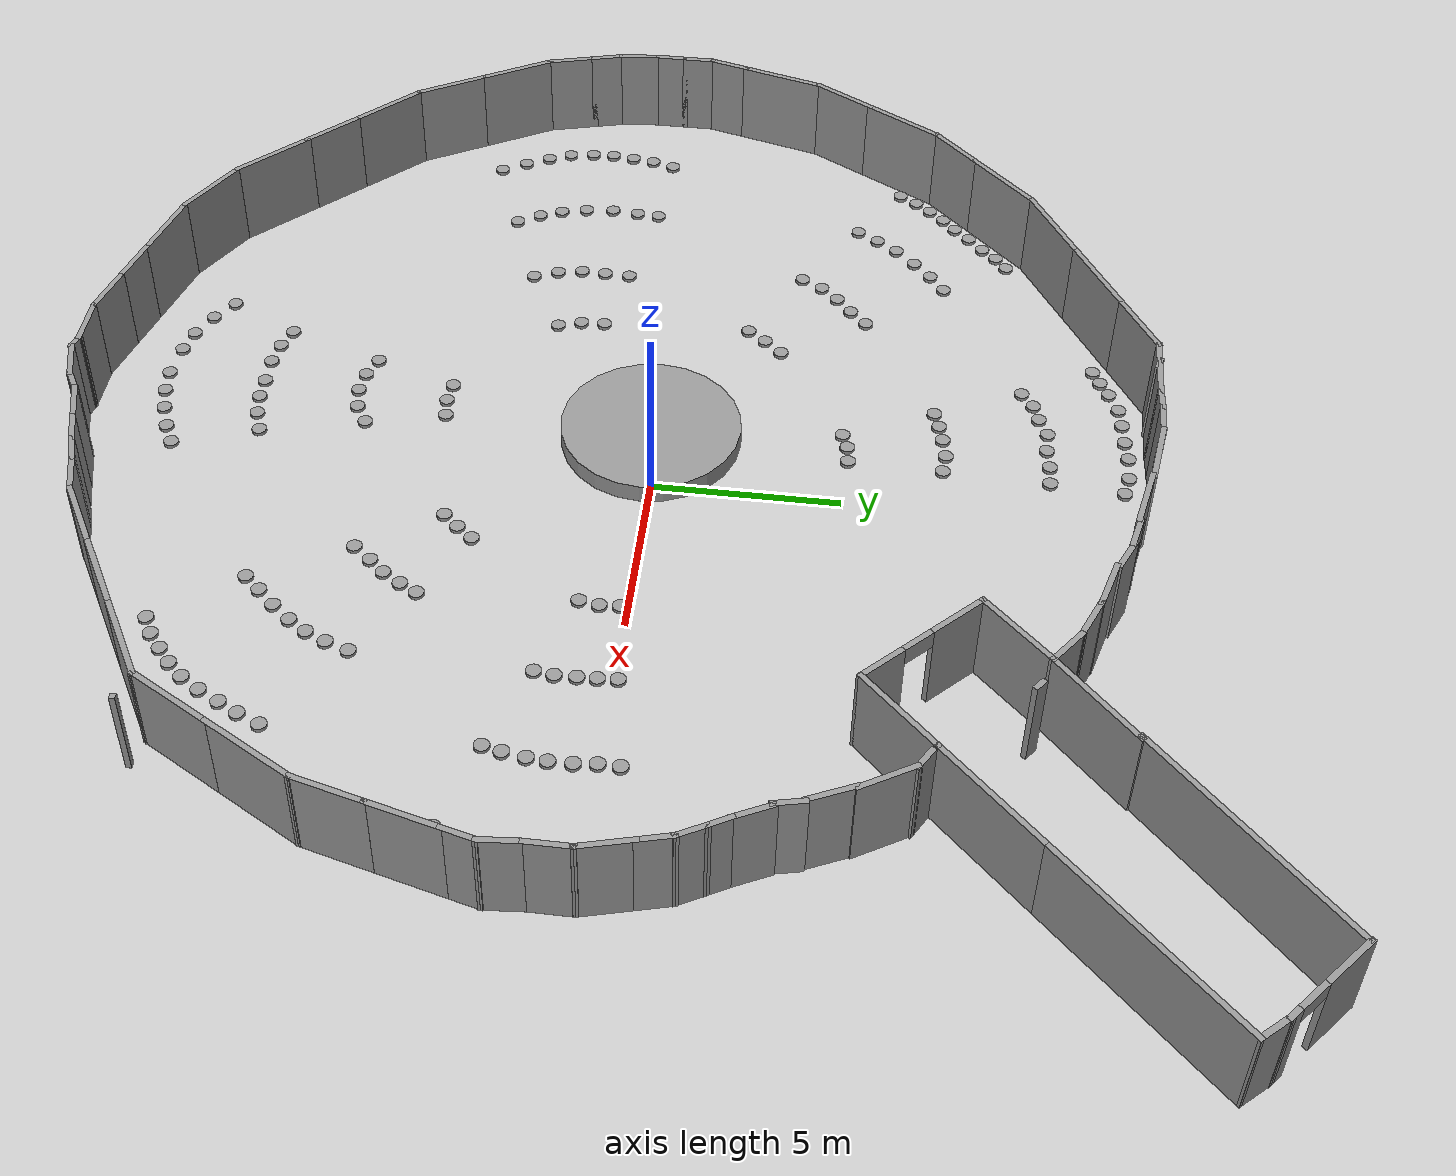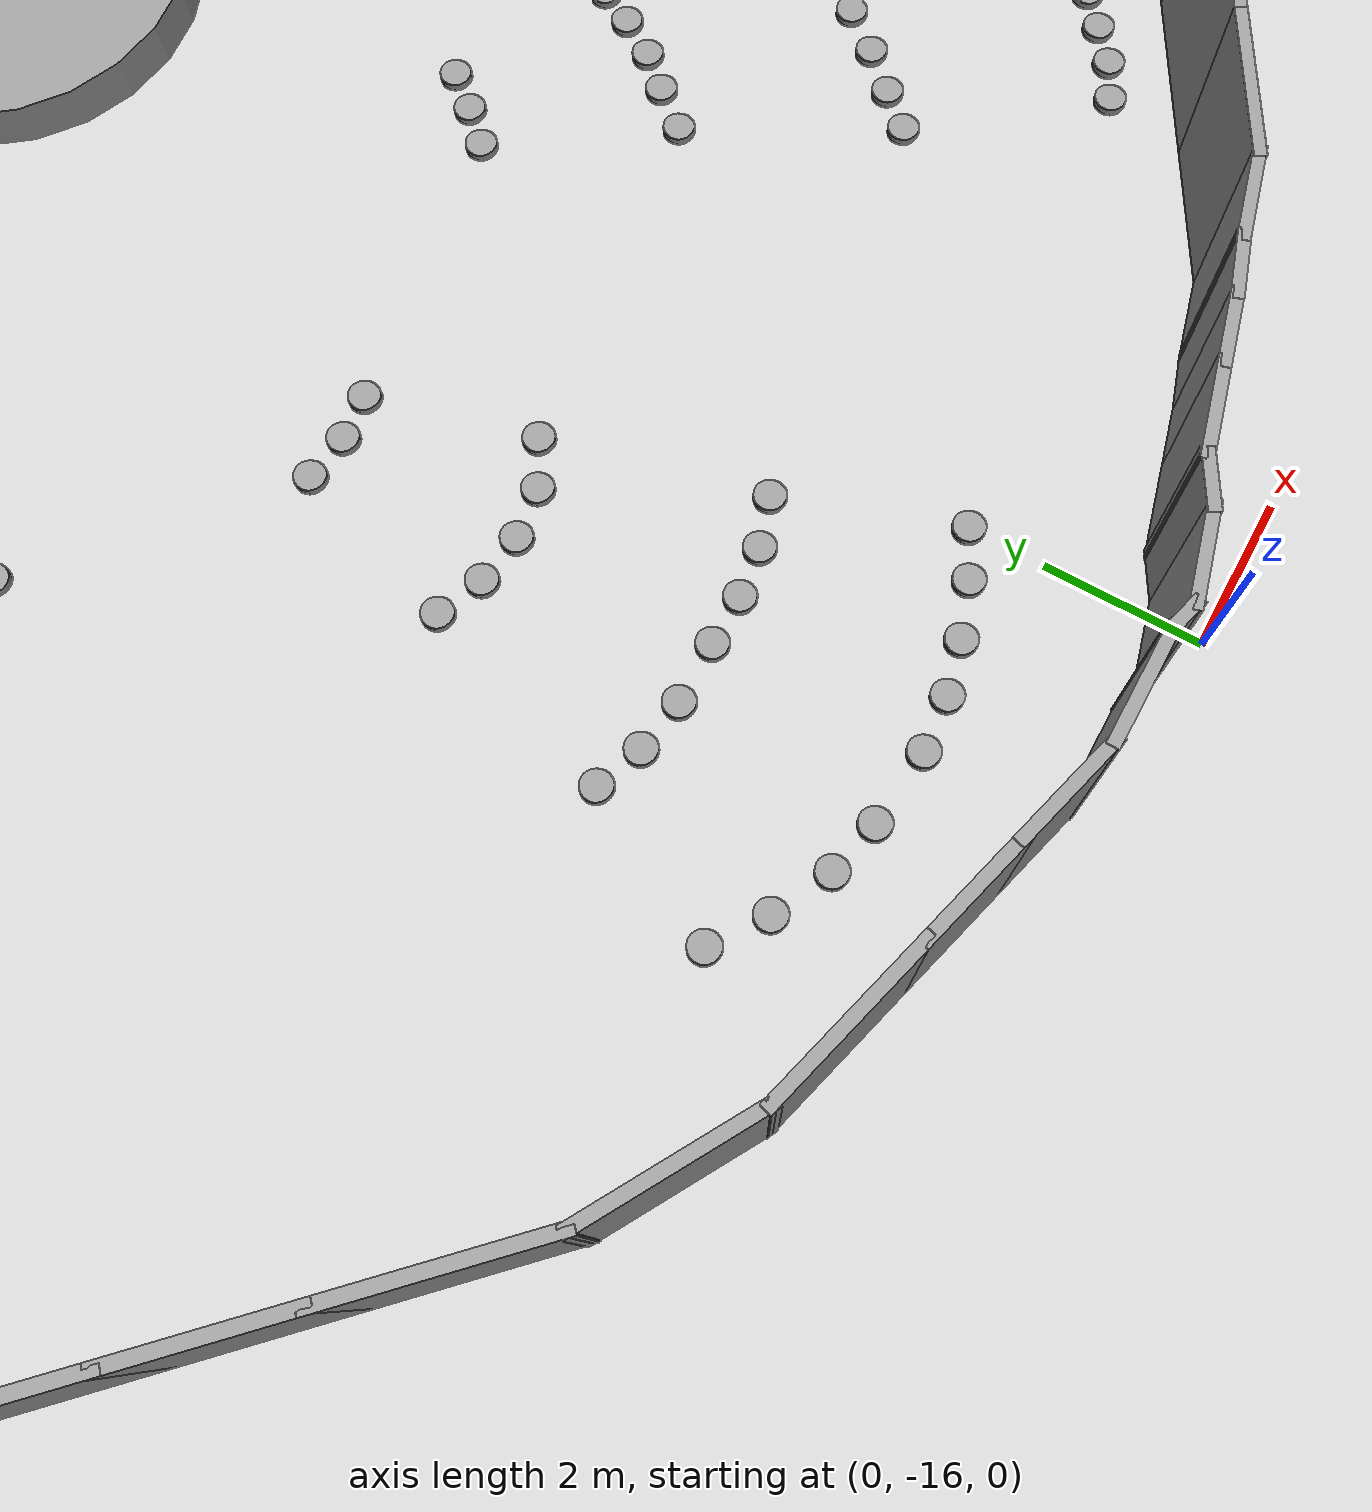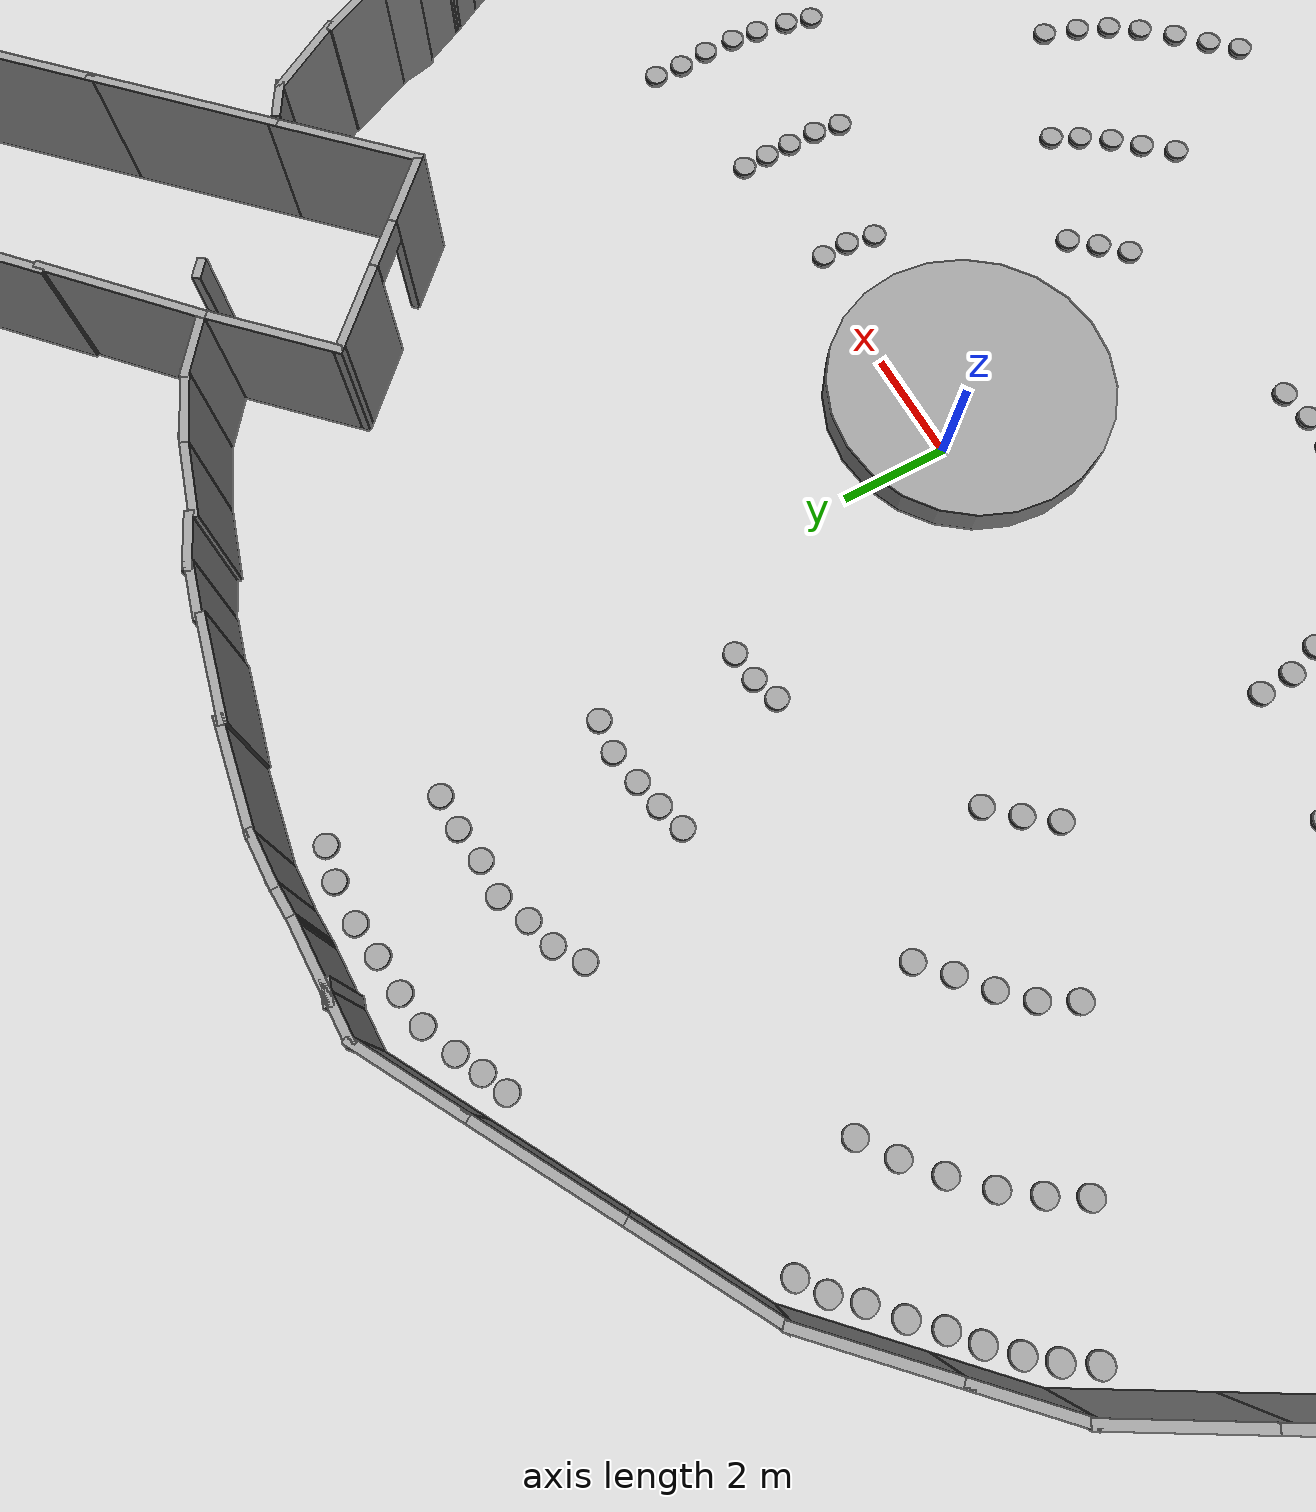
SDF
<sdf version="1.6">
 <world name="default">
  <model name="ground_plane">
   <static>1</static>
   <link name="link">
    <collision name="collision">
     <geometry><plane><normal>0 0 1</normal><size>100 100</size></plane></geometry>
     <surface><friction><ode><mu>100</mu><mu2>50</mu2></ode></friction></surface>
    </collision>
    <visual name="visual">
     <cast_shadows>0</cast_shadows>
     <geometry><plane><normal>0 0 1</normal><size>100 100</size></plane></geometry>
     <material>
      <script><uri>file://media/materials/scripts/gazebo.material</uri><name>Gazebo/Grey</name></script>
     </material>
    </visual>
   </link>
  </model>
  <gravity>0 0 -9.8</gravity>
  <magnetic_field>6e-06 2.3e-05 -4.2e-05</magnetic_field>
  <atmosphere type="adiabatic"/>
  <physics name="default_physics" default="0" type="ode">
   <max_step_size>0.001</max_step_size>
   <real_time_factor>1</real_time_factor>
   <real_time_update_rate>1000</real_time_update_rate>
  </physics>
  <scene><ambient>0.4 0.4 0.4 1</ambient><background>0.7 0.7 0.7 1</background><shadows>1</shadows></scene>
  <spherical_coordinates>
   <surface_model>EARTH_WGS84</surface_model>
   <latitude_deg>0</latitude_deg>
   <longitude_deg>0</longitude_deg>
   <elevation>0</elevation>
   <heading_deg>0</heading_deg>
  </spherical_coordinates>
  <model name="CircularFence">
   <pose>0.1565 0.6213 -0.024158 0 -0 0</pose>
   <link name="Wall_108">
    <collision name="Wall_108_Collision">
     <geometry><box><size>0.16 0.15 2.5</size></box></geometry>
     <pose>0 0 1.25 0 -0 0</pose>
    </collision>
    <visual name="Wall_108_Visual">
     <pose>0 0 1.25 0 -0 0</pose>
     <geometry><box><size>0.16 0.15 2.5</size></box></geometry>
     <material>
      <script><uri>file://media/materials/scripts/gazebo.material</uri><name>Gazebo/Grey</name></script>
      <ambient>0 0 0 0</ambient>
     </material>
    </visual>
    <pose>10.6487 -11.5681 0 0 -0 0</pose>
   </link>
   <link name="Wall_118">
    <collision name="Wall_118_Collision">
     <geometry><box><size>1.94177 0.15 2.5</size></box></geometry>
     <pose>0 0 1.25 0 -0 0</pose>
    </collision>
    <visual name="Wall_118_Visual">
     <pose>0 0 1.25 0 -0 0</pose>
     <geometry><box><size>1.94177 0.15 2.5</size></box></geometry>
     <material>
      <script><uri>file://media/materials/scripts/gazebo.material</uri><name>Gazebo/Grey</name></script>
      <ambient>1 1 1 1</ambient>
     </material>
    </visual>
    <pose>-0.537149 12.2558 0 0 -0 2.98255</pose>
   </link>
   <link name="Wall_120">
    <collision name="Wall_120_Collision">
     <geometry><box><size>1.83123 0.15 2.5</size></box></geometry>
     <pose>0 0 1.25 0 -0 0</pose>
    </collision>
    <visual name="Wall_120_Visual">
     <pose>0 0 1.25 0 -0 0</pose>
     <geometry><box><size>1.83123 0.15 2.5</size></box></geometry>
     <material>
      <script><uri>file://media/materials/scripts/gazebo.material</uri><name>Gazebo/Grey</name></script>
      <ambient>1 1 1 1</ambient>
     </material>
    </visual>
    <pose>1.13156 11.8951 0 0 -0 2.92292</pose>
   </link>
   <link name="Wall_123">
    <collision name="Wall_123_Collision">
     <geometry><box><size>1.25 0.15 2.5</size></box></geometry>
     <pose>0 0 1.25 0 -0 0</pose>
    </collision>
    <visual name="Wall_123_Visual">
     <pose>0 0 1.25 0 -0 0</pose>
     <geometry><box><size>1.25 0.15 2.5</size></box></geometry>
     <material>
      <script><uri>file://media/materials/scripts/gazebo.material</uri><name>Gazebo/Grey</name></script>
      <ambient>1 1 1 1</ambient>
     </material>
    </visual>
    <pose>13.4677 -1.09217 0 0 -0 1.5708</pose>
   </link>
   <link name="Wall_126">
    <collision name="Wall_126_Collision">
     <geometry><box><size>1.5 0.15 2.5</size></box></geometry>
     <pose>0 0 1.25 0 -0 0</pose>
    </collision>
    <visual name="Wall_126_Visual">
     <pose>0 0 1.25 0 -0 0</pose>
     <geometry><box><size>1.5 0.15 2.5</size></box></geometry>
     <material>
      <script><uri>file://media/materials/scripts/gazebo.material</uri><name>Gazebo/Grey</name></script>
      <ambient>1 1 1 1</ambient>
     </material>
    </visual>
    <pose>13.293 0.109828 0 0 -0 1.8326</pose>
   </link>
   <link name="Wall_127">
    <collision name="Wall_127_Collision">
     <geometry><box><size>1 0.15 2.5</size></box></geometry>
     <pose>0 0 1.25 0 -0 0</pose>
    </collision>
    <visual name="Wall_127_Visual">
     <pose>0 0 1.25 0 -0 0</pose>
     <geometry><box><size>1 0.15 2.5</size></box></geometry>
     <material>
      <script><uri>file://media/materials/scripts/gazebo.material</uri><name>Gazebo/Grey</name></script>
      <ambient>1 1 1 1</ambient>
     </material>
    </visual>
    <pose>13.0083 1.17235 0 0 -0 1.8326</pose>
   </link>
   <link name="Wall_128">
    <collision name="Wall_128_Collision">
     <geometry><box><size>0.888528 0.15 2.5</size></box></geometry>
     <pose>0 0 1.25 0 -0 0</pose>
    </collision>
    <visual name="Wall_128_Visual">
     <pose>0 0 1.25 0 -0 0</pose>
     <geometry><box><size>0.888528 0.15 2.5</size></box></geometry>
     <material>
      <script><uri>file://media/materials/scripts/gazebo.material</uri><name>Gazebo/Grey</name></script>
      <ambient>1 1 1 1</ambient>
     </material>
    </visual>
    <pose>12.7215 1.90706 0 0 -0 2.07005</pose>
   </link>
   <link name="Wall_129">
    <collision name="Wall_129_Collision">
     <geometry><box><size>0.75 0.15 2.5</size></box></geometry>
     <pose>0 0 1.25 0 -0 0</pose>
    </collision>
    <visual name="Wall_129_Visual">
     <pose>0 0 1.25 0 -0 0</pose>
     <geometry><box><size>0.75 0.15 2.5</size></box></geometry>
     <material>
      <script><uri>file://media/materials/scripts/gazebo.material</uri><name>Gazebo/Grey</name></script>
      <ambient>1 1 1 1</ambient>
     </material>
    </visual>
    <pose>12.3947 2.49105 0 0 -0 2.0944</pose>
   </link>
   <link name="Wall_130">
    <collision name="Wall_130_Collision">
     <geometry><box><size>1.12578 0.15 2.5</size></box></geometry>
     <pose>0 0 1.25 0 -0 0</pose>
    </collision>
    <visual name="Wall_130_Visual">
     <pose>0 0 1.25 0 -0 0</pose>
     <geometry><box><size>1.12578 0.15 2.5</size></box></geometry>
     <material>
      <script><uri>file://media/materials/scripts/gazebo.material</uri><name>Gazebo/Grey</name></script>
      <ambient>1 1 1 1</ambient>
     </material>
    </visual>
    <pose>12.026 3.18702 0 0 -0 2.03549</pose>
   </link>
   <link name="Wall_131">
    <collision name="Wall_131_Collision">
     <geometry><box><size>0.879 0.15 2.5</size></box></geometry>
     <pose>0 0 1.25 0 -0 0</pose>
    </collision>
    <visual name="Wall_131_Visual">
     <pose>0 0 1.25 0 -0 0</pose>
     <geometry><box><size>0.879 0.15 2.5</size></box></geometry>
     <material>
      <script><uri>file://media/materials/scripts/gazebo.material</uri><name>Gazebo/Grey</name></script>
      <ambient>1 1 1 1</ambient>
     </material>
    </visual>
    <pose>11.6892 3.94192 0 0 -0 1.79684</pose>
   </link>
   <link name="Wall_132">
    <collision name="Wall_132_Collision">
     <geometry><box><size>1.36585 0.15 2.5</size></box></geometry>
     <pose>0 0 1.25 0 -0 0</pose>
    </collision>
    <visual name="Wall_132_Visual">
     <pose>0 0 1.25 0 -0 0</pose>
     <geometry><box><size>1.36585 0.15 2.5</size></box></geometry>
     <material>
      <script><uri>file://media/materials/scripts/gazebo.material</uri><name>Gazebo/Grey</name></script>
      <ambient>1 1 1 1</ambient>
     </material>
    </visual>
    <pose>11.3126 4.84739 0 0 -0 2.00995</pose>
   </link>
   <link name="Wall_133">
    <collision name="Wall_133_Collision">
     <geometry><box><size>1.64734 0.15 2.5</size></box></geometry>
     <pose>0 0 1.25 0 -0 0</pose>
    </collision>
    <visual name="Wall_133_Visual">
     <pose>0 0 1.25 0 -0 0</pose>
     <geometry><box><size>1.64734 0.15 2.5</size></box></geometry>
     <material>
      <script><uri>file://media/materials/scripts/gazebo.material</uri><name>Gazebo/Grey</name></script>
      <ambient>1 1 1 1</ambient>
     </material>
    </visual>
    <pose>10.7045 6.03905 0 0 -0 2.11267</pose>
   </link>
   <link name="Wall_134">
    <collision name="Wall_134_Collision">
     <geometry><box><size>0.75 0.15 2.5</size></box></geometry>
     <pose>0 0 1.25 0 -0 0</pose>
    </collision>
    <visual name="Wall_134_Visual">
     <pose>0 0 1.25 0 -0 0</pose>
     <geometry><box><size>0.75 0.15 2.5</size></box></geometry>
     <material>
      <script><uri>file://media/materials/scripts/gazebo.material</uri><name>Gazebo/Grey</name></script>
      <ambient>1 1 1 1</ambient>
     </material>
    </visual>
    <pose>10.095 6.83046 0 0 -0 2.61799</pose>
   </link>
   <link name="Wall_138">
    <collision name="Wall_138_Collision">
     <geometry><box><size>1.24911 0.15 2.5</size></box></geometry>
     <pose>0 0 1.25 0 -0 0</pose>
    </collision>
    <visual name="Wall_138_Visual">
     <pose>0 0 1.25 0 -0 0</pose>
     <geometry><box><size>1.24911 0.15 2.5</size></box></geometry>
     <material>
      <script><uri>file://media/materials/scripts/gazebo.material</uri><name>Gazebo/Grey</name></script>
      <ambient>1 1 1 1</ambient>
     </material>
    </visual>
    <pose>6.34771 9.97388 0 0 -0 2.4965</pose>
   </link>
   <link name="Wall_139">
    <collision name="Wall_139_Collision">
     <geometry><box><size>1.31498 0.15 2.5</size></box></geometry>
     <pose>0 0 1.25 0 -0 0</pose>
    </collision>
    <visual name="Wall_139_Visual">
     <pose>0 0 1.25 0 -0 0</pose>
     <geometry><box><size>1.31498 0.15 2.5</size></box></geometry>
     <material>
      <script><uri>file://media/materials/scripts/gazebo.material</uri><name>Gazebo/Grey</name></script>
      <ambient>1 1 1 1</ambient>
     </material>
    </visual>
    <pose>5.37423 10.5362 0 0 -0 2.7322</pose>
   </link>
   <link name="Wall_140">
    <collision name="Wall_140_Collision">
     <geometry><box><size>1.49782 0.15 2.5</size></box></geometry>
     <pose>0 0 1.25 0 -0 0</pose>
    </collision>
    <visual name="Wall_140_Visual">
     <pose>0 0 1.25 0 -0 0</pose>
     <geometry><box><size>1.49782 0.15 2.5</size></box></geometry>
     <material>
      <script><uri>file://media/materials/scripts/gazebo.material</uri><name>Gazebo/Grey</name></script>
      <ambient>1 1 1 1</ambient>
     </material>
    </visual>
    <pose>4.22956 10.9573 0 0 -0 2.85692</pose>
   </link>
   <link name="Wall_141">
    <collision name="Wall_141_Collision">
     <geometry><box><size>1.00545 0.15 2.5</size></box></geometry>
     <pose>0 0 1.25 0 -0 0</pose>
    </collision>
    <visual name="Wall_141_Visual">
     <pose>0 0 1.25 0 -0 0</pose>
     <geometry><box><size>1.00545 0.15 2.5</size></box></geometry>
     <material>
      <script><uri>file://media/materials/scripts/gazebo.material</uri><name>Gazebo/Grey</name></script>
      <ambient>1 1 1 1</ambient>
     </material>
    </visual>
    <pose>3.19415 11.3982 0 0 -0 2.71064</pose>
   </link>
   <link name="Wall_142">
    <collision name="Wall_142_Collision">
     <geometry><box><size>0.993176 0.15 2.5</size></box></geometry>
     <pose>0 0 1.25 0 -0 0</pose>
    </collision>
    <visual name="Wall_142_Visual">
     <pose>0 0 1.25 0 -0 0</pose>
     <geometry><box><size>0.993176 0.15 2.5</size></box></geometry>
     <material>
      <script><uri>file://media/materials/scripts/gazebo.material</uri><name>Gazebo/Grey</name></script>
      <ambient>1 1 1 1</ambient>
     </material>
    </visual>
    <pose>2.39708 11.6448 0 0 -0 2.89134</pose>
   </link>
   <link name="Wall_144">
    <collision name="Wall_144_Collision">
     <geometry><box><size>0.5 0.15 2.5</size></box></geometry>
     <pose>0 0 1.25 0 -0 0</pose>
    </collision>
    <visual name="Wall_144_Visual">
     <pose>0 0 1.25 0 -0 0</pose>
     <geometry><box><size>0.5 0.15 2.5</size></box></geometry>
     <material>
      <script><uri>file://media/materials/scripts/gazebo.material</uri><name>Gazebo/Grey</name></script>
      <ambient>1 1 1 1</ambient>
     </material>
    </visual>
    <pose>-1.16759 -16.1719 0 0 0 -0.261799</pose>
   </link>
   <link name="Wall_145">
    <collision name="Wall_145_Collision">
     <geometry><box><size>1.25 0.15 2.5</size></box></geometry>
     <pose>0 0 1.25 0 -0 0</pose>
    </collision>
    <visual name="Wall_145_Visual">
     <pose>0 0 1.25 0 -0 0</pose>
     <geometry><box><size>1.25 0.15 2.5</size></box></geometry>
     <material>
      <script><uri>file://media/materials/scripts/gazebo.material</uri><name>Gazebo/Grey</name></script>
      <ambient>1 1 1 1</ambient>
     </material>
    </visual>
    <pose>-0.467294 -16.0748 0 0 -0 0.261799</pose>
   </link>
   <link name="Wall_146">
    <collision name="Wall_146_Collision">
     <geometry><box><size>0.75 0.15 2.5</size></box></geometry>
     <pose>0 0 1.25 0 -0 0</pose>
    </collision>
    <visual name="Wall_146_Visual">
     <pose>0 0 1.25 0 -0 0</pose>
     <geometry><box><size>0.75 0.15 2.5</size></box></geometry>
     <material>
      <script><uri>file://media/materials/scripts/gazebo.material</uri><name>Gazebo/Grey</name></script>
      <ambient>1 1 1 1</ambient>
     </material>
    </visual>
    <pose>0.323772 -15.7825 0 0 -0 0.523599</pose>
   </link>
   <link name="Wall_147">
    <collision name="Wall_147_Collision">
     <geometry><box><size>1.25 0.15 2.5</size></box></geometry>
     <pose>0 0 1.25 0 -0 0</pose>
    </collision>
    <visual name="Wall_147_Visual">
     <pose>0 0 1.25 0 -0 0</pose>
     <geometry><box><size>1.25 0.15 2.5</size></box></geometry>
     <material>
      <script><uri>file://media/materials/scripts/gazebo.material</uri><name>Gazebo/Grey</name></script>
      <ambient>1 1 1 1</ambient>
     </material>
    </visual>
    <pose>1.11484 -15.4901 0 0 -0 0.261799</pose>
   </link>
   <link name="Wall_148">
    <collision name="Wall_148_Collision">
     <geometry><box><size>1 0.15 2.5</size></box></geometry>
     <pose>0 0 1.25 0 -0 0</pose>
    </collision>
    <visual name="Wall_148_Visual">
     <pose>0 0 1.25 0 -0 0</pose>
     <geometry><box><size>1 0.15 2.5</size></box></geometry>
     <material>
      <script><uri>file://media/materials/scripts/gazebo.material</uri><name>Gazebo/Grey</name></script>
      <ambient>1 1 1 1</ambient>
     </material>
    </visual>
    <pose>2.05662 -15.2378 0 0 -0 0.261799</pose>
   </link>
   <link name="Wall_166">
    <collision name="Wall_166_Collision">
     <geometry><box><size>1.16803 0.15 2.5</size></box></geometry>
     <pose>0 0 1.25 0 -0 0</pose>
    </collision>
    <visual name="Wall_166_Visual">
     <pose>0 0 1.25 0 -0 0</pose>
     <geometry><box><size>1.16803 0.15 2.5</size></box></geometry>
     <material>
      <script><uri>file://media/materials/scripts/gazebo.material</uri><name>Gazebo/Grey</name></script>
      <ambient>1 1 1 1</ambient>
     </material>
    </visual>
    <pose>13.5088 -2.14952 0 0 -0 1.6517</pose>
   </link>
   <link name="Wall_168">
    <collision name="Wall_168_Collision">
     <geometry><box><size>0.970327 0.15 2.5</size></box></geometry>
     <pose>0 0 1.25 0 -0 0</pose>
    </collision>
    <visual name="Wall_168_Visual">
     <pose>0 0 1.25 0 -0 0</pose>
     <geometry><box><size>0.970327 0.15 2.5</size></box></geometry>
     <material>
      <script><uri>file://media/materials/scripts/gazebo.material</uri><name>Gazebo/Grey</name></script>
      <ambient>1 1 1 1</ambient>
     </material>
    </visual>
    <pose>-1.83187 12.4017 0 0 0 -0.009748</pose>
   </link>
   <link name="Wall_170">
    <collision name="Wall_170_Collision">
     <geometry><box><size>1 0.15 2.5</size></box></geometry>
     <pose>0 0 1.25 0 -0 0</pose>
    </collision>
    <visual name="Wall_170_Visual">
     <pose>0 0 1.25 0 -0 0</pose>
     <geometry><box><size>1 0.15 2.5</size></box></geometry>
     <material>
      <script><uri>file://media/materials/scripts/gazebo.material</uri><name>Gazebo/Grey</name></script>
      <ambient>1 1 1 1</ambient>
     </material>
    </visual>
    <pose>-16.3823 -1.21717 0 0 -0 1.5708</pose>
   </link>
   <link name="Wall_172">
    <collision name="Wall_172_Collision">
     <geometry><box><size>1 0.15 2.5</size></box></geometry>
     <pose>0 0 1.25 0 -0 0</pose>
    </collision>
    <visual name="Wall_172_Visual">
     <pose>0 0 1.25 0 -0 0</pose>
     <geometry><box><size>1 0.15 2.5</size></box></geometry>
     <material>
      <script><uri>file://media/materials/scripts/gazebo.material</uri><name>Gazebo/Grey</name></script>
      <ambient>1 1 1 1</ambient>
     </material>
    </visual>
    <pose>-16.3823 -2.06717 0 0 0 -1.5708</pose>
   </link>
   <link name="Wall_174">
    <collision name="Wall_174_Collision">
     <geometry><box><size>1.5 0.15 2.5</size></box></geometry>
     <pose>0 0 1.25 0 -0 0</pose>
    </collision>
    <visual name="Wall_174_Visual">
     <pose>0 0 1.25 0 -0 0</pose>
     <geometry><box><size>1.5 0.15 2.5</size></box></geometry>
     <material>
      <script><uri>file://media/materials/scripts/gazebo.material</uri><name>Gazebo/Grey</name></script>
      <ambient>1 1 1 1</ambient>
     </material>
    </visual>
    <pose>-2.01163 -16.1266 0 0 -0 3.14159</pose>
   </link>
   <link name="Wall_175">
    <collision name="Wall_175_Collision">
     <geometry><box><size>1.5 0.15 2.5</size></box></geometry>
     <pose>0 0 1.25 0 -0 0</pose>
    </collision>
    <visual name="Wall_175_Visual">
     <pose>0 0 1.25 0 -0 0</pose>
     <geometry><box><size>1.5 0.15 2.5</size></box></geometry>
     <material>
      <script><uri>file://media/materials/scripts/gazebo.material</uri><name>Gazebo/Grey</name></script>
      <ambient>1 1 1 1</ambient>
     </material>
    </visual>
    <pose>-3.33863 -15.9519 0 0 -0 2.87979</pose>
   </link>
   <link name="Wall_176">
    <collision name="Wall_176_Collision">
     <geometry><box><size>1.5 0.15 2.5</size></box></geometry>
     <pose>0 0 1.25 0 -0 0</pose>
    </collision>
    <visual name="Wall_176_Visual">
     <pose>0 0 1.25 0 -0 0</pose>
     <geometry><box><size>1.5 0.15 2.5</size></box></geometry>
     <material>
      <script><uri>file://media/materials/scripts/gazebo.material</uri><name>Gazebo/Grey</name></script>
      <ambient>1 1 1 1</ambient>
     </material>
    </visual>
    <pose>-4.64263 -15.6025 0 0 -0 2.87979</pose>
   </link>
   <link name="Wall_177">
    <collision name="Wall_177_Collision">
     <geometry><box><size>2.25 0.15 2.5</size></box></geometry>
     <pose>0 0 1.25 0 -0 0</pose>
    </collision>
    <visual name="Wall_177_Visual">
     <pose>0 0 1.25 0 -0 0</pose>
     <geometry><box><size>2.25 0.15 2.5</size></box></geometry>
     <material>
      <script><uri>file://media/materials/scripts/gazebo.material</uri><name>Gazebo/Grey</name></script>
      <ambient>1 1 1 1</ambient>
     </material>
    </visual>
    <pose>-6.30885 -15.156 0 0 -0 2.87979</pose>
   </link>
   <link name="Wall_178">
    <collision name="Wall_178_Collision">
     <geometry><box><size>2.25 0.15 2.5</size></box></geometry>
     <pose>0 0 1.25 0 -0 0</pose>
    </collision>
    <visual name="Wall_178_Visual">
     <pose>0 0 1.25 0 -0 0</pose>
     <geometry><box><size>2.25 0.15 2.5</size></box></geometry>
     <material>
      <script><uri>file://media/materials/scripts/gazebo.material</uri><name>Gazebo/Grey</name></script>
      <ambient>1 1 1 1</ambient>
     </material>
    </visual>
    <pose>-8.2324 -14.3592 0 0 -0 2.61799</pose>
   </link>
   <link name="Wall_179">
    <collision name="Wall_179_Collision">
     <geometry><box><size>2.5 0.15 2.5</size></box></geometry>
     <pose>0 0 1.25 0 -0 0</pose>
    </collision>
    <visual name="Wall_179_Visual">
     <pose>0 0 1.25 0 -0 0</pose>
     <geometry><box><size>2.5 0.15 2.5</size></box></geometry>
     <material>
      <script><uri>file://media/materials/scripts/gazebo.material</uri><name>Gazebo/Grey</name></script>
      <ambient>1 1 1 1</ambient>
     </material>
    </visual>
    <pose>-9.97258 -13.0034 0 0 -0 2.35619</pose>
   </link>
   <link name="Wall_180">
    <collision name="Wall_180_Collision">
     <geometry><box><size>2 0.15 2.5</size></box></geometry>
     <pose>0 0 1.25 0 -0 0</pose>
    </collision>
    <visual name="Wall_180_Visual">
     <pose>0 0 1.25 0 -0 0</pose>
     <geometry><box><size>2 0.15 2.5</size></box></geometry>
     <material>
      <script><uri>file://media/materials/scripts/gazebo.material</uri><name>Gazebo/Grey</name></script>
      <ambient>1 1 1 1</ambient>
     </material>
    </visual>
    <pose>-11.4575 -11.5185 0 0 -0 2.35619</pose>
   </link>
   <link name="Wall_181">
    <collision name="Wall_181_Collision">
     <geometry><box><size>2.25 0.15 2.5</size></box></geometry>
     <pose>0 0 1.25 0 -0 0</pose>
    </collision>
    <visual name="Wall_181_Visual">
     <pose>0 0 1.25 0 -0 0</pose>
     <geometry><box><size>2.25 0.15 2.5</size></box></geometry>
     <material>
      <script><uri>file://media/materials/scripts/gazebo.material</uri><name>Gazebo/Grey</name></script>
      <ambient>1 1 1 1</ambient>
     </material>
    </visual>
    <pose>-12.854 -10.1219 0 0 -0 2.35619</pose>
   </link>
   <link name="Wall_182">
    <collision name="Wall_182_Collision">
     <geometry><box><size>2.25 0.15 2.5</size></box></geometry>
     <pose>0 0 1.25 0 -0 0</pose>
    </collision>
    <visual name="Wall_182_Visual">
     <pose>0 0 1.25 0 -0 0</pose>
     <geometry><box><size>2.25 0.15 2.5</size></box></geometry>
     <material>
      <script><uri>file://media/materials/scripts/gazebo.material</uri><name>Gazebo/Grey</name></script>
      <ambient>1 1 1 1</ambient>
     </material>
    </visual>
    <pose>-14.1215 -8.47014 0 0 -0 2.0944</pose>
   </link>
   <link name="Wall_183">
    <collision name="Wall_183_Collision">
     <geometry><box><size>2.25 0.15 2.5</size></box></geometry>
     <pose>0 0 1.25 0 -0 0</pose>
    </collision>
    <visual name="Wall_183_Visual">
     <pose>0 0 1.25 0 -0 0</pose>
     <geometry><box><size>2.25 0.15 2.5</size></box></geometry>
     <material>
      <script><uri>file://media/materials/scripts/gazebo.material</uri><name>Gazebo/Grey</name></script>
      <ambient>1 1 1 1</ambient>
     </material>
    </visual>
    <pose>-15.1715 -6.65149 0 0 -0 2.0944</pose>
   </link>
   <link name="Wall_184">
    <collision name="Wall_184_Collision">
     <geometry><box><size>1.5 0.15 2.5</size></box></geometry>
     <pose>0 0 1.25 0 -0 0</pose>
    </collision>
    <visual name="Wall_184_Visual">
     <pose>0 0 1.25 0 -0 0</pose>
     <geometry><box><size>1.5 0.15 2.5</size></box></geometry>
     <material>
      <script><uri>file://media/materials/scripts/gazebo.material</uri><name>Gazebo/Grey</name></script>
      <ambient>1 1 1 1</ambient>
     </material>
    </visual>
    <pose>-15.8712 -5.09016 0 0 -0 1.8326</pose>
   </link>
   <link name="Wall_185">
    <collision name="Wall_185_Collision">
     <geometry><box><size>1 0.15 2.5</size></box></geometry>
     <pose>0 0 1.25 0 -0 0</pose>
    </collision>
    <visual name="Wall_185_Visual">
     <pose>0 0 1.25 0 -0 0</pose>
     <geometry><box><size>1 0.15 2.5</size></box></geometry>
     <material>
      <script><uri>file://media/materials/scripts/gazebo.material</uri><name>Gazebo/Grey</name></script>
      <ambient>1 1 1 1</ambient>
     </material>
    </visual>
    <pose>-16.1559 -4.02765 0 0 -0 1.8326</pose>
   </link>
   <link name="Wall_186">
    <collision name="Wall_186_Collision">
     <geometry><box><size>1.28097 0.15 2.5</size></box></geometry>
     <pose>0 0 1.25 0 -0 0</pose>
    </collision>
    <visual name="Wall_186_Visual">
     <pose>0 0 1.25 0 -0 0</pose>
     <geometry><box><size>1.28097 0.15 2.5</size></box></geometry>
     <material>
      <script><uri>file://media/materials/scripts/gazebo.material</uri><name>Gazebo/Grey</name></script>
      <ambient>1 1 1 1</ambient>
     </material>
    </visual>
    <pose>-16.3241 -3.05465 0 0 -0 1.67393</pose>
   </link>
   <link name="Wall_190">
    <collision name="Wall_190_Collision">
     <geometry><box><size>0.415491 0.15 2.5</size></box></geometry>
     <pose>0 0 1.25 0 -0 0</pose>
    </collision>
    <visual name="Wall_190_Visual">
     <pose>0 0 1.25 0 -0 0</pose>
     <geometry><box><size>0.415491 0.15 2.5</size></box></geometry>
     <material>
      <script><uri>file://media/materials/scripts/gazebo.material</uri><name>Gazebo/Grey</name></script>
      <ambient>0 0 0 0</ambient>
     </material>
    </visual>
    <pose>-3.96438 12.3692 0 0 0 -0.278323</pose>
   </link>
   <link name="Wall_200">
    <collision name="Wall_200_Collision">
     <geometry><box><size>1.25 0.15 2.5</size></box></geometry>
     <pose>0 0 1.25 0 -0 0</pose>
    </collision>
    <visual name="Wall_200_Visual">
     <pose>0 0 1.25 0 -0 0</pose>
     <geometry><box><size>1.25 0.15 2.5</size></box></geometry>
     <material>
      <script><uri>file://media/materials/scripts/gazebo.material</uri><name>Gazebo/Grey</name></script>
      <ambient>1 1 1 1</ambient>
     </material>
    </visual>
    <pose>-16.24 -0.260912 0 0 -0 1.309</pose>
   </link>
   <link name="Wall_201">
    <collision name="Wall_201_Collision">
     <geometry><box><size>2.5 0.15 2.5</size></box></geometry>
     <pose>0 0 1.25 0 -0 0</pose>
    </collision>
    <visual name="Wall_201_Visual">
     <pose>0 0 1.25 0 -0 0</pose>
     <geometry><box><size>2.5 0.15 2.5</size></box></geometry>
     <material>
      <script><uri>file://media/materials/scripts/gazebo.material</uri><name>Gazebo/Grey</name></script>
      <ambient>1 1 1 1</ambient>
     </material>
    </visual>
    <pose>-15.7935 1.40531 0 0 -0 1.309</pose>
   </link>
   <link name="Wall_202">
    <collision name="Wall_202_Collision">
     <geometry><box><size>2 0.15 2.5</size></box></geometry>
     <pose>0 0 1.25 0 -0 0</pose>
    </collision>
    <visual name="Wall_202_Visual">
     <pose>0 0 1.25 0 -0 0</pose>
     <geometry><box><size>2 0.15 2.5</size></box></geometry>
     <material>
      <script><uri>file://media/materials/scripts/gazebo.material</uri><name>Gazebo/Grey</name></script>
      <ambient>1 1 1 1</ambient>
     </material>
    </visual>
    <pose>-15.0269 3.34135 0 0 -0 1.0472</pose>
   </link>
   <link name="Wall_203">
    <collision name="Wall_203_Collision">
     <geometry><box><size>2.5 0.15 2.5</size></box></geometry>
     <pose>0 0 1.25 0 -0 0</pose>
    </collision>
    <visual name="Wall_203_Visual">
     <pose>0 0 1.25 0 -0 0</pose>
     <geometry><box><size>2.5 0.15 2.5</size></box></geometry>
     <material>
      <script><uri>file://media/materials/scripts/gazebo.material</uri><name>Gazebo/Grey</name></script>
      <ambient>1 1 1 1</ambient>
     </material>
    </visual>
    <pose>-13.9769 5.16 0 0 -0 1.0472</pose>
   </link>
   <link name="Wall_204">
    <collision name="Wall_204_Collision">
     <geometry><box><size>1.75 0.15 2.5</size></box></geometry>
     <pose>0 0 1.25 0 -0 0</pose>
    </collision>
    <visual name="Wall_204_Visual">
     <pose>0 0 1.25 0 -0 0</pose>
     <geometry><box><size>1.75 0.15 2.5</size></box></geometry>
     <material>
      <script><uri>file://media/materials/scripts/gazebo.material</uri><name>Gazebo/Grey</name></script>
      <ambient>1 1 1 1</ambient>
     </material>
    </visual>
    <pose>-12.8237 6.74327 0 0 -0 0.785398</pose>
   </link>
   <link name="Wall_205">
    <collision name="Wall_205_Collision">
     <geometry><box><size>2.5 0.15 2.5</size></box></geometry>
     <pose>0 0 1.25 0 -0 0</pose>
    </collision>
    <visual name="Wall_205_Visual">
     <pose>0 0 1.25 0 -0 0</pose>
     <geometry><box><size>2.5 0.15 2.5</size></box></geometry>
     <material>
      <script><uri>file://media/materials/scripts/gazebo.material</uri><name>Gazebo/Grey</name></script>
      <ambient>1 1 1 1</ambient>
     </material>
    </visual>
    <pose>-11.4272 8.1398 0 0 -0 0.785398</pose>
   </link>
   <link name="Wall_206">
    <collision name="Wall_206_Collision">
     <geometry><box><size>2.5 0.15 2.5</size></box></geometry>
     <pose>0 0 1.25 0 -0 0</pose>
    </collision>
    <visual name="Wall_206_Visual">
     <pose>0 0 1.25 0 -0 0</pose>
     <geometry><box><size>2.5 0.15 2.5</size></box></geometry>
     <material>
      <script><uri>file://media/materials/scripts/gazebo.material</uri><name>Gazebo/Grey</name></script>
      <ambient>1 1 1 1</ambient>
     </material>
    </visual>
    <pose>-9.57876 9.55815 0 0 -0 0.523599</pose>
   </link>
   <link name="Wall_207">
    <collision name="Wall_207_Collision">
     <geometry><box><size>2.75 0.15 2.5</size></box></geometry>
     <pose>0 0 1.25 0 -0 0</pose>
    </collision>
    <visual name="Wall_207_Visual">
     <pose>0 0 1.25 0 -0 0</pose>
     <geometry><box><size>2.75 0.15 2.5</size></box></geometry>
     <material>
      <script><uri>file://media/materials/scripts/gazebo.material</uri><name>Gazebo/Grey</name></script>
      <ambient>1 1 1 1</ambient>
     </material>
    </visual>
    <pose>-7.43534 10.7957 0 0 -0 0.523599</pose>
   </link>
   <link name="Wall_208">
    <collision name="Wall_208_Collision">
     <geometry><box><size>2 0.15 2.5</size></box></geometry>
     <pose>0 0 1.25 0 -0 0</pose>
    </collision>
    <visual name="Wall_208_Visual">
     <pose>0 0 1.25 0 -0 0</pose>
     <geometry><box><size>2 0.15 2.5</size></box></geometry>
     <material>
      <script><uri>file://media/materials/scripts/gazebo.material</uri><name>Gazebo/Grey</name></script>
      <ambient>1 1 1 1</ambient>
     </material>
    </visual>
    <pose>-5.50844 11.9081 0 0 -0 0.523599</pose>
   </link>
   <link name="Wall_209">
    <collision name="Wall_209_Collision">
     <geometry><box><size>2 0.15 2.5</size></box></geometry>
     <pose>0 0 1.25 0 -0 0</pose>
    </collision>
    <visual name="Wall_209_Visual">
     <pose>0 0 1.25 0 -0 0</pose>
     <geometry><box><size>2 0.15 2.5</size></box></geometry>
     <material>
      <script><uri>file://media/materials/scripts/gazebo.material</uri><name>Gazebo/Grey</name></script>
      <ambient>1 1 1 1</ambient>
     </material>
    </visual>
    <pose>-3.78236 12.3707 0 0 -0 0</pose>
   </link>
   <link name="Wall_210">
    <collision name="Wall_210_Collision">
     <geometry><box><size>0.766345 0.15 2.5</size></box></geometry>
     <pose>0 0 1.25 0 -0 0</pose>
    </collision>
    <visual name="Wall_210_Visual">
     <pose>0 0 1.25 0 -0 0</pose>
     <geometry><box><size>0.766345 0.15 2.5</size></box></geometry>
     <material>
      <script><uri>file://media/materials/scripts/gazebo.material</uri><name>Gazebo/Grey</name></script>
      <ambient>1 1 1 1</ambient>
     </material>
    </visual>
    <pose>-2.54969 12.3882 0 0 -0 0.056841</pose>
   </link>
   <link name="Wall_212">
    <collision name="Wall_212_Collision">
     <geometry><box><size>1 0.15 2.5</size></box></geometry>
     <pose>0 0 1.25 0 -0 0</pose>
    </collision>
    <visual name="Wall_212_Visual">
     <pose>0 0 1.25 0 -0 0</pose>
     <geometry><box><size>1 0.15 2.5</size></box></geometry>
     <material>
      <script><uri>file://media/materials/scripts/gazebo.material</uri><name>Gazebo/Grey</name></script>
      <ambient>1 1 1 1</ambient>
     </material>
    </visual>
    <pose>13.4399 -3.06739 0 0 0 -1.8326</pose>
   </link>
   <link name="Wall_213">
    <collision name="Wall_213_Collision">
     <geometry><box><size>2 0.15 2.5</size></box></geometry>
     <pose>0 0 1.25 0 -0 0</pose>
    </collision>
    <visual name="Wall_213_Visual">
     <pose>0 0 1.25 0 -0 0</pose>
     <geometry><box><size>2 0.15 2.5</size></box></geometry>
     <material>
      <script><uri>file://media/materials/scripts/gazebo.material</uri><name>Gazebo/Grey</name></script>
      <ambient>1 1 1 1</ambient>
     </material>
    </visual>
    <pose>13.0905 -4.37139 0 0 0 -1.8326</pose>
   </link>
   <link name="Wall_214">
    <collision name="Wall_214_Collision">
     <geometry><box><size>2 0.15 2.5</size></box></geometry>
     <pose>0 0 1.25 0 -0 0</pose>
    </collision>
    <visual name="Wall_214_Visual">
     <pose>0 0 1.25 0 -0 0</pose>
     <geometry><box><size>2 0.15 2.5</size></box></geometry>
     <material>
      <script><uri>file://media/materials/scripts/gazebo.material</uri><name>Gazebo/Grey</name></script>
      <ambient>1 1 1 1</ambient>
     </material>
    </visual>
    <pose>12.6117 -6.15835 0 0 0 -1.8326</pose>
   </link>
   <link name="Wall_215">
    <collision name="Wall_215_Collision">
     <geometry><box><size>2.75 0.15 2.5</size></box></geometry>
     <pose>0 0 1.25 0 -0 0</pose>
    </collision>
    <visual name="Wall_215_Visual">
     <pose>0 0 1.25 0 -0 0</pose>
     <geometry><box><size>2.75 0.15 2.5</size></box></geometry>
     <material>
      <script><uri>file://media/materials/scripts/gazebo.material</uri><name>Gazebo/Grey</name></script>
      <ambient>1 1 1 1</ambient>
     </material>
    </visual>
    <pose>11.7223 -8.17767 0 0 0 -2.0944</pose>
   </link>
   <link name="Wall_216">
    <collision name="Wall_216_Collision">
     <geometry><box><size>2.5 0.15 2.5</size></box></geometry>
     <pose>0 0 1.25 0 -0 0</pose>
    </collision>
    <visual name="Wall_216_Visual">
     <pose>0 0 1.25 0 -0 0</pose>
     <geometry><box><size>2.5 0.15 2.5</size></box></geometry>
     <material>
      <script><uri>file://media/materials/scripts/gazebo.material</uri><name>Gazebo/Grey</name></script>
      <ambient>1 1 1 1</ambient>
     </material>
    </visual>
    <pose>10.4848 -10.3211 0 0 0 -2.0944</pose>
   </link>
   <link name="Wall_217">
    <collision name="Wall_217_Collision">
     <geometry><box><size>2.5 0.15 2.5</size></box></geometry>
     <pose>0 0 1.25 0 -0 0</pose>
    </collision>
    <visual name="Wall_217_Visual">
     <pose>0 0 1.25 0 -0 0</pose>
     <geometry><box><size>2.5 0.15 2.5</size></box></geometry>
     <material>
      <script><uri>file://media/materials/scripts/gazebo.material</uri><name>Gazebo/Grey</name></script>
      <ambient>1 1 1 1</ambient>
     </material>
    </visual>
    <pose>8.87974 -11.9262 0 0 0 -2.61799</pose>
   </link>
   <link name="Wall_218">
    <collision name="Wall_218_Collision">
     <geometry><box><size>2.5 0.15 2.5</size></box></geometry>
     <pose>0 0 1.25 0 -0 0</pose>
    </collision>
    <visual name="Wall_218_Visual">
     <pose>0 0 1.25 0 -0 0</pose>
     <geometry><box><size>2.5 0.15 2.5</size></box></geometry>
     <material>
      <script><uri>file://media/materials/scripts/gazebo.material</uri><name>Gazebo/Grey</name></script>
      <ambient>1 1 1 1</ambient>
     </material>
    </visual>
    <pose>6.84458 -13.1012 0 0 0 -2.61799</pose>
   </link>
   <link name="Wall_219">
    <collision name="Wall_219_Collision">
     <geometry><box><size>2 0.15 2.5</size></box></geometry>
     <pose>0 0 1.25 0 -0 0</pose>
    </collision>
    <visual name="Wall_219_Visual">
     <pose>0 0 1.25 0 -0 0</pose>
     <geometry><box><size>2 0.15 2.5</size></box></geometry>
     <material>
      <script><uri>file://media/materials/scripts/gazebo.material</uri><name>Gazebo/Grey</name></script>
      <ambient>1 1 1 1</ambient>
     </material>
    </visual>
    <pose>5.02592 -14.1512 0 0 0 -2.61799</pose>
   </link>
   <link name="Wall_220">
    <collision name="Wall_220_Collision">
     <geometry><box><size>1.25 0.15 2.5</size></box></geometry>
     <pose>0 0 1.25 0 -0 0</pose>
    </collision>
    <visual name="Wall_220_Visual">
     <pose>0 0 1.25 0 -0 0</pose>
     <geometry><box><size>1.25 0.15 2.5</size></box></geometry>
     <material>
      <script><uri>file://media/materials/scripts/gazebo.material</uri><name>Gazebo/Grey</name></script>
      <ambient>1 1 1 1</ambient>
     </material>
    </visual>
    <pose>3.69359 -14.756 0 0 0 -2.87979</pose>
   </link>
   <link name="Wall_221">
    <collision name="Wall_221_Collision">
     <geometry><box><size>0.882068 0.15 2.5</size></box></geometry>
     <pose>0 0 1.25 0 -0 0</pose>
    </collision>
    <visual name="Wall_221_Visual">
     <pose>0 0 1.25 0 -0 0</pose>
     <geometry><box><size>0.882068 0.15 2.5</size></box></geometry>
     <material>
      <script><uri>file://media/materials/scripts/gazebo.material</uri><name>Gazebo/Grey</name></script>
      <ambient>1 1 1 1</ambient>
     </material>
    </visual>
    <pose>2.81473 -15.0131 0 0 0 -2.82286</pose>
   </link>
   <link name="Wall_224">
    <collision name="Wall_224_Collision">
     <geometry><box><size>2.5 0.15 2.5</size></box></geometry>
     <pose>0 0 1.25 0 -0 0</pose>
    </collision>
    <visual name="Wall_224_Visual">
     <pose>0 0 1.25 0 -0 0</pose>
     <geometry><box><size>2.5 0.15 2.5</size></box></geometry>
     <material>
      <script><uri>file://media/materials/scripts/gazebo.material</uri><name>Gazebo/Grey</name></script>
      <ambient>1 1 1 1</ambient>
     </material>
    </visual>
    <pose>5.95598 8.8126 0 0 0 -2.35619</pose>
   </link>
   <link name="Wall_225">
    <pose>6.48631 6.62057 0 0 0 -0.785398</pose>
    <visual name="Wall_225_Visual_0">
     <pose>-1.14631 0 1.25 0 -0 0</pose>
     <geometry><box><size>1.70738 0.15 2.5</size></box></geometry>
     <material>
      <script><uri>file://media/materials/scripts/gazebo.material</uri><name>Gazebo/Grey</name></script>
      <ambient>1 1 1 1</ambient>
     </material>
    </visual>
    <collision name="Wall_225_Collision_0">
     <geometry><box><size>1.70738 0.15 2.5</size></box></geometry>
     <pose>-1.14631 0 1.25 0 -0 0</pose>
    </collision>
    <visual name="Wall_225_Visual_1">
     <pose>1.30369 0 1.25 0 -0 0</pose>
     <geometry><box><size>1.39262 0.15 2.5</size></box></geometry>
     <material>
      <script><uri>file://media/materials/scripts/gazebo.material</uri><name>Gazebo/Grey</name></script>
      <ambient>1 1 1 1</ambient>
     </material>
    </visual>
    <collision name="Wall_225_Collision_1">
     <geometry><box><size>1.39262 0.15 2.5</size></box></geometry>
     <pose>1.30369 0 1.25 0 -0 0</pose>
    </collision>
    <visual name="Wall_225_Visual_2">
     <pose>0.157377 0 2.25 0 -0 0</pose>
     <geometry><box><size>0.9 0.15 0.5</size></box></geometry>
     <material>
      <script><uri>file://media/materials/scripts/gazebo.material</uri><name>Gazebo/Grey</name></script>
      <ambient>1 1 1 1</ambient>
     </material>
    </visual>
    <collision name="Wall_225_Collision_2">
     <geometry><box><size>0.9 0.15 0.5</size></box></geometry>
     <pose>0.157377 0 2.25 0 -0 0</pose>
    </collision>
   </link>
   <link name="Wall_226">
    <collision name="Wall_226_Collision">
     <geometry><box><size>2.75 0.15 2.5</size></box></geometry>
     <pose>0 0 1.25 0 -0 0</pose>
    </collision>
    <visual name="Wall_226_Visual">
     <pose>0 0 1.25 0 -0 0</pose>
     <geometry><box><size>2.75 0.15 2.5</size></box></geometry>
     <material>
      <script><uri>file://media/materials/scripts/gazebo.material</uri><name>Gazebo/Grey</name></script>
      <ambient>1 1 1 1</ambient>
     </material>
    </visual>
    <pose>8.76673 6.17863 0 0 -0 0.785398</pose>
   </link>
   <link name="Wall_228">
    <collision name="Wall_228_Collision">
     <geometry><box><size>0.387432 0.15 2.5</size></box></geometry>
     <pose>0 0 1.25 0 -0 0</pose>
    </collision>
    <visual name="Wall_228_Visual">
     <pose>0 0 1.25 0 -0 0</pose>
     <geometry><box><size>0.387432 0.15 2.5</size></box></geometry>
     <material>
      <script><uri>file://media/materials/scripts/gazebo.material</uri><name>Gazebo/Grey</name></script>
      <ambient>0 0 0 0</ambient>
     </material>
    </visual>
    <pose>7.59944 9.34213 0 0 -0 2.48023</pose>
   </link>
   <link name="Wall_230">
    <collision name="Wall_230_Collision">
     <geometry><box><size>3.04553 0.15 2.5</size></box></geometry>
     <pose>0 0 1.25 0 -0 0</pose>
    </collision>
    <visual name="Wall_230_Visual">
     <pose>0 0 1.25 0 -0 0</pose>
     <geometry><box><size>3.04553 0.15 2.5</size></box></geometry>
     <material>
      <script><uri>file://media/materials/scripts/gazebo.material</uri><name>Gazebo/Grey</name></script>
      <ambient>1 1 1 1</ambient>
     </material>
    </visual>
    <pose>7.84637 10.6301 0 0 0 -2.39183</pose>
   </link>
   <link name="Wall_233">
    <collision name="Wall_233_Collision">
     <geometry><box><size>3.5 0.15 2.5</size></box></geometry>
     <pose>0 0 1.25 0 -0 0</pose>
    </collision>
    <visual name="Wall_233_Visual">
     <pose>0 0 1.25 0 -0 0</pose>
     <geometry><box><size>3.5 0.15 2.5</size></box></geometry>
     <material>
      <script><uri>file://media/materials/scripts/gazebo.material</uri><name>Gazebo/Grey</name></script>
      <ambient>1 1 1 1</ambient>
     </material>
    </visual>
    <pose>10.8704 8.28227 0 0 -0 0.785398</pose>
   </link>
   <link name="Wall_235">
    <pose>14.764 15.305 0 0 -0 2.43116</pose>
    <visual name="Wall_235_Visual_0">
     <pose>-1.24215 0 1.25 0 -0 0</pose>
     <geometry><box><size>0.420278 0.15 2.5</size></box></geometry>
     <material>
      <script><uri>file://media/materials/scripts/gazebo.material</uri><name>Gazebo/Grey</name></script>
      <ambient>1 1 1 1</ambient>
     </material>
    </visual>
    <collision name="Wall_235_Collision_0">
     <geometry><box><size>0.420278 0.15 2.5</size></box></geometry>
     <pose>-1.24215 0 1.25 0 -0 0</pose>
    </collision>
    <visual name="Wall_235_Visual_1">
     <pose>0.660139 0 1.25 0 -0 0</pose>
     <geometry><box><size>1.5843 0.15 2.5</size></box></geometry>
     <material>
      <script><uri>file://media/materials/scripts/gazebo.material</uri><name>Gazebo/Grey</name></script>
      <ambient>1 1 1 1</ambient>
     </material>
    </visual>
    <collision name="Wall_235_Collision_1">
     <geometry><box><size>1.5843 0.15 2.5</size></box></geometry>
     <pose>0.660139 0 1.25 0 -0 0</pose>
    </collision>
    <visual name="Wall_235_Visual_2">
     <pose>-0.582012 0 2.25 0 -0 0</pose>
     <geometry><box><size>0.9 0.15 0.5</size></box></geometry>
     <material>
      <script><uri>file://media/materials/scripts/gazebo.material</uri><name>Gazebo/Grey</name></script>
      <ambient>1 1 1 1</ambient>
     </material>
    </visual>
    <collision name="Wall_235_Collision_2">
     <geometry><box><size>0.9 0.15 0.5</size></box></geometry>
     <pose>-0.582012 0 2.25 0 -0 0</pose>
    </collision>
   </link>
   <link name="Wall_236">
    <collision name="Wall_236_Collision">
     <geometry><box><size>6.82723 0.15 2.5</size></box></geometry>
     <pose>0 0 1.25 0 -0 0</pose>
    </collision>
    <visual name="Wall_236_Visual">
     <pose>0 0 1.25 0 -0 0</pose>
     <geometry><box><size>6.82723 0.15 2.5</size></box></geometry>
     <material>
      <script><uri>file://media/materials/scripts/gazebo.material</uri><name>Gazebo/Grey</name></script>
      <ambient>1 1 1 1</ambient>
     </material>
    </visual>
    <pose>11.2764 13.8917 0 0 0 -2.39187</pose>
   </link>
   <link name="Wall_238">
    <collision name="Wall_238_Collision">
     <geometry><box><size>6.25 0.15 2.5</size></box></geometry>
     <pose>0 0 1.25 0 -0 0</pose>
    </collision>
    <visual name="Wall_238_Visual">
     <pose>0 0 1.25 0 -0 0</pose>
     <geometry><box><size>6.25 0.15 2.5</size></box></geometry>
     <material>
      <script><uri>file://media/materials/scripts/gazebo.material</uri><name>Gazebo/Grey</name></script>
      <ambient>1 1 1 1</ambient>
     </material>
    </visual>
    <pose>14.2115 11.6234 0 0 -0 0.785398</pose>
   </link>
   <link name="Wall_239">
    <collision name="Wall_239_Collision">
     <geometry><box><size>0.990548 0.15 2.5</size></box></geometry>
     <pose>0 0 1.25 0 -0 0</pose>
    </collision>
    <visual name="Wall_239_Visual">
     <pose>0 0 1.25 0 -0 0</pose>
     <geometry><box><size>0.990548 0.15 2.5</size></box></geometry>
     <material>
      <script><uri>file://media/materials/scripts/gazebo.material</uri><name>Gazebo/Grey</name></script>
      <ambient>1 1 1 1</ambient>
     </material>
    </visual>
    <pose>16.0881 14.0934 0 0 -0 2.30002</pose>
   </link>
   <static>1</static>
  </model>
  <model name="unit_cylinder_1_clone_clone_13_clone_56_clone_34_clone">
   <pose>12.1937 0.267663 0.048249 0 -0 0.015201</pose>
   <link name="link">
    <inertial>
     <mass>1</mass>
     <inertia><ixx>0.145833</ixx><ixy>0</ixy><ixz>0</ixz><iyy>0.145833</iyy><iyz>0</iyz><izz>0.125</izz></inertia>
    </inertial>
    <collision name="collision">
     <geometry><cylinder><radius>0.20005</radius><length>0.0965019</length></cylinder></geometry>
    </collision>
    <visual name="visual">
     <geometry><cylinder><radius>0.20005</radius><length>0.0965019</length></cylinder></geometry>
     <material>
      <script><name>Gazebo/Grey</name><uri>file://media/materials/scripts/gazebo.material</uri></script>
     </material>
    </visual>
   </link>
  </model>
  <model name="unit_cylinder_1_clone_clone_13_clone_56_clone_34_clone_0">
   <pose>12.2409 -0.320365 0.048249 0 -0 0.015201</pose>
   <link name="link">
    <inertial>
     <mass>1</mass>
     <inertia><ixx>0.145833</ixx><ixy>0</ixy><ixz>0</ixz><iyy>0.145833</iyy><iyz>0</iyz><izz>0.125</izz></inertia>
    </inertial>
    <collision name="collision">
     <geometry><cylinder><radius>0.20005</radius><length>0.0965019</length></cylinder></geometry>
    </collision>
    <visual name="visual">
     <geometry><cylinder><radius>0.20005</radius><length>0.0965019</length></cylinder></geometry>
     <material>
      <script><name>Gazebo/Grey</name><uri>file://media/materials/scripts/gazebo.material</uri></script>
     </material>
    </visual>
   </link>
  </model>
  <model name="unit_cylinder_1_clone_clone_13_clone_56_clone_34_clone_1">
   <pose>12.3164 -0.925131 0.048249 0 -0 0.015201</pose>
   <link name="link">
    <inertial>
     <mass>1</mass>
     <inertia><ixx>0.145833</ixx><ixy>0</ixy><ixz>0</ixz><iyy>0.145833</iyy><iyz>0</iyz><izz>0.125</izz></inertia>
    </inertial>
    <collision name="collision">
     <geometry><cylinder><radius>0.20005</radius><length>0.0965019</length></cylinder></geometry>
    </collision>
    <visual name="visual">
     <geometry><cylinder><radius>0.20005</radius><length>0.0965019</length></cylinder></geometry>
     <material>
      <script><name>Gazebo/Grey</name><uri>file://media/materials/scripts/gazebo.material</uri></script>
     </material>
    </visual>
   </link>
  </model>
  <model name="unit_cylinder_1_clone_clone_13_clone_56_clone_34_clone_2">
   <pose>12.3143 -1.4792 0.048244 0 -0 0.015201</pose>
   <link name="link">
    <inertial>
     <mass>1</mass>
     <inertia><ixx>0.145833</ixx><ixy>0</ixy><ixz>0</ixz><iyy>0.145833</iyy><iyz>0</iyz><izz>0.125</izz></inertia>
    </inertial>
    <collision name="collision">
     <geometry><cylinder><radius>0.20005</radius><length>0.0965019</length></cylinder></geometry>
    </collision>
    <visual name="visual">
     <geometry><cylinder><radius>0.20005</radius><length>0.0965019</length></cylinder></geometry>
     <material>
      <script><name>Gazebo/Grey</name><uri>file://media/materials/scripts/gazebo.material</uri></script>
     </material>
    </visual>
   </link>
  </model>
  <model name="unit_cylinder_1_clone_clone_13_clone_56_clone_34_clone_3">
   <pose>12.2819 -2.01723 0.048243 -2e-06 2e-06 0.015201</pose>
   <link name="link">
    <inertial>
     <mass>1</mass>
     <inertia><ixx>0.145833</ixx><ixy>0</ixy><ixz>0</ixz><iyy>0.145833</iyy><iyz>0</iyz><izz>0.125</izz></inertia>
    </inertial>
    <collision name="collision">
     <geometry><cylinder><radius>0.20005</radius><length>0.0965019</length></cylinder></geometry>
    </collision>
    <visual name="visual">
     <geometry><cylinder><radius>0.20005</radius><length>0.0965019</length></cylinder></geometry>
     <material>
      <script><name>Gazebo/Grey</name><uri>file://media/materials/scripts/gazebo.material</uri></script>
     </material>
    </visual>
   </link>
  </model>
  <model name="unit_cylinder_1_clone_clone_13_clone_56_clone_34_clone_4">
   <pose>12.2142 -2.49039 0.048243 -2e-06 2e-06 0.015201</pose>
   <link name="link">
    <inertial>
     <mass>1</mass>
     <inertia><ixx>0.145833</ixx><ixy>0</ixy><ixz>0</ixz><iyy>0.145833</iyy><iyz>0</iyz><izz>0.125</izz></inertia>
    </inertial>
    <collision name="collision">
     <geometry><cylinder><radius>0.20005</radius><length>0.0965019</length></cylinder></geometry>
    </collision>
    <visual name="visual">
     <geometry><cylinder><radius>0.20005</radius><length>0.0965019</length></cylinder></geometry>
     <material>
      <script><name>Gazebo/Grey</name><uri>file://media/materials/scripts/gazebo.material</uri></script>
     </material>
    </visual>
   </link>
  </model>
  <model name="unit_cylinder_1_clone_clone_13_clone_56_clone_34_clone_5">
   <pose>12 -3 0.048249 1e-06 -1e-06 0.015201</pose>
   <link name="link">
    <inertial>
     <mass>1</mass>
     <inertia><ixx>0.145833</ixx><ixy>0</ixy><ixz>0</ixz><iyy>0.145833</iyy><iyz>0</iyz><izz>0.125</izz></inertia>
    </inertial>
    <collision name="collision">
     <geometry><cylinder><radius>0.20005</radius><length>0.0965019</length></cylinder></geometry>
    </collision>
    <visual name="visual">
     <geometry><cylinder><radius>0.20005</radius><length>0.0965019</length></cylinder></geometry>
     <material>
      <script><name>Gazebo/Grey</name><uri>file://media/materials/scripts/gazebo.material</uri></script>
     </material>
    </visual>
   </link>
  </model>
  <model name="unit_cylinder_1_clone_clone_13_clone_56_clone_34_clone_6">
   <pose>11.7319 -3.52736 0.048249 1e-06 -1e-06 0.015201</pose>
   <link name="link">
    <inertial>
     <mass>1</mass>
     <inertia><ixx>0.145833</ixx><ixy>0</ixy><ixz>0</ixz><iyy>0.145833</iyy><iyz>0</iyz><izz>0.125</izz></inertia>
    </inertial>
    <collision name="collision">
     <geometry><cylinder><radius>0.20005</radius><length>0.0965019</length></cylinder></geometry>
    </collision>
    <visual name="visual">
     <geometry><cylinder><radius>0.20005</radius><length>0.0965019</length></cylinder></geometry>
     <material>
      <script><name>Gazebo/Grey</name><uri>file://media/materials/scripts/gazebo.material</uri></script>
     </material>
    </visual>
   </link>
  </model>
  <model name="unit_cylinder_1_clone_clone_13_clone_56_clone_34_clone_8">
   <pose>9.44024 -0.044123 0.048245 0 -0 0.015201</pose>
   <link name="link">
    <inertial>
     <mass>1</mass>
     <inertia><ixx>0.145833</ixx><ixy>0</ixy><ixz>0</ixz><iyy>0.145833</iyy><iyz>0</iyz><izz>0.125</izz></inertia>
    </inertial>
    <collision name="collision">
     <geometry><cylinder><radius>0.20005</radius><length>0.0965019</length></cylinder></geometry>
    </collision>
    <visual name="visual">
     <geometry><cylinder><radius>0.20005</radius><length>0.0965019</length></cylinder></geometry>
     <material>
      <script><name>Gazebo/Grey</name><uri>file://media/materials/scripts/gazebo.material</uri></script>
     </material>
    </visual>
   </link>
  </model>
  <model name="unit_cylinder_1_clone_clone_13_clone_56_clone_34_clone_9">
   <pose>9.50201 -0.618001 0.048249 1e-06 -1e-06 0.015201</pose>
   <link name="link">
    <inertial>
     <mass>1</mass>
     <inertia><ixx>0.145833</ixx><ixy>0</ixy><ixz>0</ixz><iyy>0.145833</iyy><iyz>0</iyz><izz>0.125</izz></inertia>
    </inertial>
    <collision name="collision">
     <geometry><cylinder><radius>0.20005</radius><length>0.0965019</length></cylinder></geometry>
    </collision>
    <visual name="visual">
     <geometry><cylinder><radius>0.20005</radius><length>0.0965019</length></cylinder></geometry>
     <material>
      <script><name>Gazebo/Grey</name><uri>file://media/materials/scripts/gazebo.material</uri></script>
     </material>
    </visual>
   </link>
  </model>
  <model name="unit_cylinder_1_clone_clone_13_clone_56_clone_34_clone_10">
   <pose>9.50697 -1.22259 0.048243 -1e-06 1e-06 0.015201</pose>
   <link name="link">
    <inertial>
     <mass>1</mass>
     <inertia><ixx>0.145833</ixx><ixy>0</ixy><ixz>0</ixz><iyy>0.145833</iyy><iyz>0</iyz><izz>0.125</izz></inertia>
    </inertial>
    <collision name="collision">
     <geometry><cylinder><radius>0.20005</radius><length>0.0965019</length></cylinder></geometry>
    </collision>
    <visual name="visual">
     <geometry><cylinder><radius>0.20005</radius><length>0.0965019</length></cylinder></geometry>
     <material>
      <script><name>Gazebo/Grey</name><uri>file://media/materials/scripts/gazebo.material</uri></script>
     </material>
    </visual>
   </link>
  </model>
  <model name="unit_cylinder_1_clone_clone_13_clone_56_clone_34_clone_11">
   <pose>9.46183 -1.74553 0.048243 -1e-06 1e-06 0.015201</pose>
   <link name="link">
    <inertial>
     <mass>1</mass>
     <inertia><ixx>0.145833</ixx><ixy>0</ixy><ixz>0</ixz><iyy>0.145833</iyy><iyz>0</iyz><izz>0.125</izz></inertia>
    </inertial>
    <collision name="collision">
     <geometry><cylinder><radius>0.20005</radius><length>0.0965019</length></cylinder></geometry>
    </collision>
    <visual name="visual">
     <geometry><cylinder><radius>0.20005</radius><length>0.0965019</length></cylinder></geometry>
     <material>
      <script><name>Gazebo/Grey</name><uri>file://media/materials/scripts/gazebo.material</uri></script>
     </material>
    </visual>
   </link>
  </model>
  <model name="unit_cylinder_1_clone_clone_13_clone_56_clone_34_clone_12">
   <pose>9.36305 -2.34871 0.048249 0 -0 0.015201</pose>
   <link name="link">
    <inertial>
     <mass>1</mass>
     <inertia><ixx>0.145833</ixx><ixy>0</ixy><ixz>0</ixz><iyy>0.145833</iyy><iyz>0</iyz><izz>0.125</izz></inertia>
    </inertial>
    <collision name="collision">
     <geometry><cylinder><radius>0.20005</radius><length>0.0965019</length></cylinder></geometry>
    </collision>
    <visual name="visual">
     <geometry><cylinder><radius>0.20005</radius><length>0.0965019</length></cylinder></geometry>
     <material>
      <script><name>Gazebo/Grey</name><uri>file://media/materials/scripts/gazebo.material</uri></script>
     </material>
    </visual>
   </link>
  </model>
  <model name="unit_cylinder_1_clone_clone_13_clone_56_clone_34_clone_13">
   <pose>9.23829 -2.84355 0.048244 0 -0 1.35588</pose>
   <link name="link">
    <inertial>
     <mass>1</mass>
     <inertia><ixx>0.145833</ixx><ixy>0</ixy><ixz>0</ixz><iyy>0.145833</iyy><iyz>0</iyz><izz>0.125</izz></inertia>
    </inertial>
    <collision name="collision">
     <geometry><cylinder><radius>0.20005</radius><length>0.0965019</length></cylinder></geometry>
    </collision>
    <visual name="visual">
     <geometry><cylinder><radius>0.20005</radius><length>0.0965019</length></cylinder></geometry>
     <material>
      <script><name>Gazebo/Grey</name><uri>file://media/materials/scripts/gazebo.material</uri></script>
     </material>
    </visual>
   </link>
  </model>
  <model name="unit_cylinder_1_clone_clone_13_clone_56_clone_34_clone_14">
   <pose>6.80065 0.0717 0.048249 0 -0 0.015201</pose>
   <link name="link">
    <inertial>
     <mass>1</mass>
     <inertia><ixx>0.145833</ixx><ixy>0</ixy><ixz>0</ixz><iyy>0.145833</iyy><iyz>0</iyz><izz>0.125</izz></inertia>
    </inertial>
    <collision name="collision">
     <geometry><cylinder><radius>0.20005</radius><length>0.0965019</length></cylinder></geometry>
    </collision>
    <visual name="visual">
     <geometry><cylinder><radius>0.20005</radius><length>0.0965019</length></cylinder></geometry>
     <material>
      <script><name>Gazebo/Grey</name><uri>file://media/materials/scripts/gazebo.material</uri></script>
     </material>
    </visual>
   </link>
  </model>
  <model name="unit_cylinder_1_clone_clone_13_clone_56_clone_34_clone_15">
   <pose>6.83326 -0.435253 0.048249 0 -0 0.015201</pose>
   <link name="link">
    <inertial>
     <mass>1</mass>
     <inertia><ixx>0.145833</ixx><ixy>0</ixy><ixz>0</ixz><iyy>0.145833</iyy><iyz>0</iyz><izz>0.125</izz></inertia>
    </inertial>
    <collision name="collision">
     <geometry><cylinder><radius>0.20005</radius><length>0.0965019</length></cylinder></geometry>
    </collision>
    <visual name="visual">
     <geometry><cylinder><radius>0.20005</radius><length>0.0965019</length></cylinder></geometry>
     <material>
      <script><name>Gazebo/Grey</name><uri>file://media/materials/scripts/gazebo.material</uri></script>
     </material>
    </visual>
   </link>
  </model>
  <model name="unit_cylinder_1_clone_clone_13_clone_56_clone_34_clone_16">
   <pose>6.84672 -0.934954 0.048243 -1e-06 1e-06 0.015201</pose>
   <link name="link">
    <inertial>
     <mass>1</mass>
     <inertia><ixx>0.145833</ixx><ixy>0</ixy><ixz>0</ixz><iyy>0.145833</iyy><iyz>0</iyz><izz>0.125</izz></inertia>
    </inertial>
    <collision name="collision">
     <geometry><cylinder><radius>0.20005</radius><length>0.0965019</length></cylinder></geometry>
    </collision>
    <visual name="visual">
     <geometry><cylinder><radius>0.20005</radius><length>0.0965019</length></cylinder></geometry>
     <material>
      <script><name>Gazebo/Grey</name><uri>file://media/materials/scripts/gazebo.material</uri></script>
     </material>
    </visual>
   </link>
  </model>
  <model name="unit_cylinder_1_clone_clone_13_clone_56_clone_34_clone_17">
   <pose>6.8579 -1.49385 0.048249 0 -0 0.015201</pose>
   <link name="link">
    <inertial>
     <mass>1</mass>
     <inertia><ixx>0.145833</ixx><ixy>0</ixy><ixz>0</ixz><iyy>0.145833</iyy><iyz>0</iyz><izz>0.125</izz></inertia>
    </inertial>
    <collision name="collision">
     <geometry><cylinder><radius>0.20005</radius><length>0.0965019</length></cylinder></geometry>
    </collision>
    <visual name="visual">
     <geometry><cylinder><radius>0.20005</radius><length>0.0965019</length></cylinder></geometry>
     <material>
      <script><name>Gazebo/Grey</name><uri>file://media/materials/scripts/gazebo.material</uri></script>
     </material>
    </visual>
   </link>
  </model>
  <model name="unit_cylinder_1_clone_clone_13_clone_56_clone_34_clone_18">
   <pose>6.78655 -2.00858 0.048249 0 -0 0.015201</pose>
   <link name="link">
    <inertial>
     <mass>1</mass>
     <inertia><ixx>0.145833</ixx><ixy>0</ixy><ixz>0</ixz><iyy>0.145833</iyy><iyz>0</iyz><izz>0.125</izz></inertia>
    </inertial>
    <collision name="collision">
     <geometry><cylinder><radius>0.20005</radius><length>0.0965019</length></cylinder></geometry>
    </collision>
    <visual name="visual">
     <geometry><cylinder><radius>0.20005</radius><length>0.0965019</length></cylinder></geometry>
     <material>
      <script><name>Gazebo/Grey</name><uri>file://media/materials/scripts/gazebo.material</uri></script>
     </material>
    </visual>
   </link>
  </model>
  <model name="unit_cylinder_1_clone_clone_13_clone_56_clone_34_clone_19">
   <pose>4.39979 -0.211784 0.048249 0 -0 0.015201</pose>
   <link name="link">
    <inertial>
     <mass>1</mass>
     <inertia><ixx>0.145833</ixx><ixy>0</ixy><ixz>0</ixz><iyy>0.145833</iyy><iyz>0</iyz><izz>0.125</izz></inertia>
    </inertial>
    <collision name="collision">
     <geometry><cylinder><radius>0.20005</radius><length>0.0965019</length></cylinder></geometry>
    </collision>
    <visual name="visual">
     <geometry><cylinder><radius>0.20005</radius><length>0.0965019</length></cylinder></geometry>
     <material>
      <script><name>Gazebo/Grey</name><uri>file://media/materials/scripts/gazebo.material</uri></script>
     </material>
    </visual>
   </link>
  </model>
  <model name="unit_cylinder_1_clone_clone_13_clone_56_clone_34_clone_20">
   <pose>4.43692 -0.735738 0.048243 -1e-06 1e-06 0.015201</pose>
   <link name="link">
    <inertial>
     <mass>1</mass>
     <inertia><ixx>0.145833</ixx><ixy>0</ixy><ixz>0</ixz><iyy>0.145833</iyy><iyz>0</iyz><izz>0.125</izz></inertia>
    </inertial>
    <collision name="collision">
     <geometry><cylinder><radius>0.20005</radius><length>0.0965019</length></cylinder></geometry>
    </collision>
    <visual name="visual">
     <geometry><cylinder><radius>0.20005</radius><length>0.0965019</length></cylinder></geometry>
     <material>
      <script><name>Gazebo/Grey</name><uri>file://media/materials/scripts/gazebo.material</uri></script>
     </material>
    </visual>
   </link>
  </model>
  <model name="unit_cylinder_1_clone_clone_13_clone_56_clone_34_clone_21">
   <pose>4.34042 -1.26685 0.048243 -1e-06 1e-06 0.015201</pose>
   <link name="link">
    <inertial>
     <mass>1</mass>
     <inertia><ixx>0.145833</ixx><ixy>0</ixy><ixz>0</ixz><iyy>0.145833</iyy><iyz>0</iyz><izz>0.125</izz></inertia>
    </inertial>
    <collision name="collision">
     <geometry><cylinder><radius>0.20005</radius><length>0.0965019</length></cylinder></geometry>
    </collision>
    <visual name="visual">
     <geometry><cylinder><radius>0.20005</radius><length>0.0965019</length></cylinder></geometry>
     <material>
      <script><name>Gazebo/Grey</name><uri>file://media/materials/scripts/gazebo.material</uri></script>
     </material>
    </visual>
   </link>
  </model>
  <model name="unit_cylinder_1_clone_clone_13_clone_56_clone_34_clone_22">
   <pose>2.53514 -4.33414 0.048247 0 -0 0.015201</pose>
   <link name="link">
    <inertial>
     <mass>1</mass>
     <inertia><ixx>0.145833</ixx><ixy>0</ixy><ixz>0</ixz><iyy>0.145833</iyy><iyz>0</iyz><izz>0.125</izz></inertia>
    </inertial>
    <collision name="collision">
     <geometry><cylinder><radius>0.20005</radius><length>0.0965019</length></cylinder></geometry>
    </collision>
    <visual name="visual">
     <geometry><cylinder><radius>0.20005</radius><length>0.0965019</length></cylinder></geometry>
     <material>
      <script><name>Gazebo/Grey</name><uri>file://media/materials/scripts/gazebo.material</uri></script>
     </material>
    </visual>
   </link>
  </model>
  <model name="unit_cylinder_1_clone_clone_13_clone_56_clone_34_clone_23">
   <pose>2.16905 -4.77365 0.048247 0 -0 0.015201</pose>
   <link name="link">
    <inertial>
     <mass>1</mass>
     <inertia><ixx>0.145833</ixx><ixy>0</ixy><ixz>0</ixz><iyy>0.145833</iyy><iyz>0</iyz><izz>0.125</izz></inertia>
    </inertial>
    <collision name="collision">
     <geometry><cylinder><radius>0.20005</radius><length>0.0965019</length></cylinder></geometry>
    </collision>
    <visual name="visual">
     <geometry><cylinder><radius>0.20005</radius><length>0.0965019</length></cylinder></geometry>
     <material>
      <script><name>Gazebo/Grey</name><uri>file://media/materials/scripts/gazebo.material</uri></script>
     </material>
    </visual>
   </link>
  </model>
  <model name="unit_cylinder_1_clone_clone_13_clone_56_clone_34_clone_24">
   <pose>1.77694 -5.19106 0.048244 0 -0 0.015201</pose>
   <link name="link">
    <inertial>
     <mass>1</mass>
     <inertia><ixx>0.145833</ixx><ixy>0</ixy><ixz>0</ixz><iyy>0.145833</iyy><iyz>0</iyz><izz>0.125</izz></inertia>
    </inertial>
    <collision name="collision">
     <geometry><cylinder><radius>0.20005</radius><length>0.0965019</length></cylinder></geometry>
    </collision>
    <visual name="visual">
     <geometry><cylinder><radius>0.20005</radius><length>0.0965019</length></cylinder></geometry>
     <material>
      <script><name>Gazebo/Grey</name><uri>file://media/materials/scripts/gazebo.material</uri></script>
     </material>
    </visual>
   </link>
  </model>
  <model name="unit_cylinder_1_clone_clone_13_clone_56_clone_34_clone_25">
   <pose>4.59389 -5.35942 0.048247 0 -0 0.015201</pose>
   <link name="link">
    <inertial>
     <mass>1</mass>
     <inertia><ixx>0.145833</ixx><ixy>0</ixy><ixz>0</ixz><iyy>0.145833</iyy><iyz>0</iyz><izz>0.125</izz></inertia>
    </inertial>
    <collision name="collision">
     <geometry><cylinder><radius>0.20005</radius><length>0.0965019</length></cylinder></geometry>
    </collision>
    <visual name="visual">
     <geometry><cylinder><radius>0.20005</radius><length>0.0965019</length></cylinder></geometry>
     <material>
      <script><name>Gazebo/Grey</name><uri>file://media/materials/scripts/gazebo.material</uri></script>
     </material>
    </visual>
   </link>
  </model>
  <model name="unit_cylinder_1_clone_clone_13_clone_56_clone_34_clone_26">
   <pose>4.33174 -5.83668 0.048247 0 -0 0.015201</pose>
   <link name="link">
    <inertial>
     <mass>1</mass>
     <inertia><ixx>0.145833</ixx><ixy>0</ixy><ixz>0</ixz><iyy>0.145833</iyy><iyz>0</iyz><izz>0.125</izz></inertia>
    </inertial>
    <collision name="collision">
     <geometry><cylinder><radius>0.20005</radius><length>0.0965019</length></cylinder></geometry>
    </collision>
    <visual name="visual">
     <geometry><cylinder><radius>0.20005</radius><length>0.0965019</length></cylinder></geometry>
     <material>
      <script><name>Gazebo/Grey</name><uri>file://media/materials/scripts/gazebo.material</uri></script>
     </material>
    </visual>
   </link>
  </model>
  <model name="unit_cylinder_1_clone_clone_13_clone_56_clone_34_clone_27">
   <pose>4.00831 -6.33458 0.048244 0 -0 0.015201</pose>
   <link name="link">
    <inertial>
     <mass>1</mass>
     <inertia><ixx>0.145833</ixx><ixy>0</ixy><ixz>0</ixz><iyy>0.145833</iyy><iyz>0</iyz><izz>0.125</izz></inertia>
    </inertial>
    <collision name="collision">
     <geometry><cylinder><radius>0.20005</radius><length>0.0965019</length></cylinder></geometry>
    </collision>
    <visual name="visual">
     <geometry><cylinder><radius>0.20005</radius><length>0.0965019</length></cylinder></geometry>
     <material>
      <script><name>Gazebo/Grey</name><uri>file://media/materials/scripts/gazebo.material</uri></script>
     </material>
    </visual>
   </link>
  </model>
  <model name="unit_cylinder_1_clone_clone_13_clone_56_clone_34_clone_28">
   <pose>3.62072 -6.76158 0.048244 0 -0 0.015201</pose>
   <link name="link">
    <inertial>
     <mass>1</mass>
     <inertia><ixx>0.145833</ixx><ixy>0</ixy><ixz>0</ixz><iyy>0.145833</iyy><iyz>0</iyz><izz>0.125</izz></inertia>
    </inertial>
    <collision name="collision">
     <geometry><cylinder><radius>0.20005</radius><length>0.0965019</length></cylinder></geometry>
    </collision>
    <visual name="visual">
     <geometry><cylinder><radius>0.20005</radius><length>0.0965019</length></cylinder></geometry>
     <material>
      <script><name>Gazebo/Grey</name><uri>file://media/materials/scripts/gazebo.material</uri></script>
     </material>
    </visual>
   </link>
  </model>
  <model name="unit_cylinder_1_clone_clone_13_clone_56_clone_34_clone_29">
   <pose>3.20719 -7.2577 0.048247 0 -0 0.015201</pose>
   <link name="link">
    <inertial>
     <mass>1</mass>
     <inertia><ixx>0.145833</ixx><ixy>0</ixy><ixz>0</ixz><iyy>0.145833</iyy><iyz>0</iyz><izz>0.125</izz></inertia>
    </inertial>
    <collision name="collision">
     <geometry><cylinder><radius>0.20005</radius><length>0.0965019</length></cylinder></geometry>
    </collision>
    <visual name="visual">
     <geometry><cylinder><radius>0.20005</radius><length>0.0965019</length></cylinder></geometry>
     <material>
      <script><name>Gazebo/Grey</name><uri>file://media/materials/scripts/gazebo.material</uri></script>
     </material>
    </visual>
   </link>
  </model>
  <model name="unit_cylinder_1_clone_clone_13_clone_56_clone_34_clone_30">
   <pose>6.71083 -6.63281 0.048247 0 -0 0.015201</pose>
   <link name="link">
    <inertial>
     <mass>1</mass>
     <inertia><ixx>0.145833</ixx><ixy>0</ixy><ixz>0</ixz><iyy>0.145833</iyy><iyz>0</iyz><izz>0.125</izz></inertia>
    </inertial>
    <collision name="collision">
     <geometry><cylinder><radius>0.20005</radius><length>0.0965019</length></cylinder></geometry>
    </collision>
    <visual name="visual">
     <geometry><cylinder><radius>0.20005</radius><length>0.0965019</length></cylinder></geometry>
     <material>
      <script><name>Gazebo/Grey</name><uri>file://media/materials/scripts/gazebo.material</uri></script>
     </material>
    </visual>
   </link>
  </model>
  <model name="unit_cylinder_1_clone_clone_13_clone_56_clone_34_clone_31">
   <pose>6.49472 -7.25896 0.048246 1e-06 -1e-06 0.015201</pose>
   <link name="link">
    <inertial>
     <mass>1</mass>
     <inertia><ixx>0.145833</ixx><ixy>0</ixy><ixz>0</ixz><iyy>0.145833</iyy><iyz>0</iyz><izz>0.125</izz></inertia>
    </inertial>
    <collision name="collision">
     <geometry><cylinder><radius>0.20005</radius><length>0.0965019</length></cylinder></geometry>
    </collision>
    <visual name="visual">
     <geometry><cylinder><radius>0.20005</radius><length>0.0965019</length></cylinder></geometry>
     <material>
      <script><name>Gazebo/Grey</name><uri>file://media/materials/scripts/gazebo.material</uri></script>
     </material>
    </visual>
   </link>
  </model>
  <model name="unit_cylinder_1_clone_clone_13_clone_56_clone_34_clone_32">
   <pose>6.23642 -7.81752 0.048246 1e-06 -1e-06 0.015201</pose>
   <link name="link">
    <inertial>
     <mass>1</mass>
     <inertia><ixx>0.145833</ixx><ixy>0</ixy><ixz>0</ixz><iyy>0.145833</iyy><iyz>0</iyz><izz>0.125</izz></inertia>
    </inertial>
    <collision name="collision">
     <geometry><cylinder><radius>0.20005</radius><length>0.0965019</length></cylinder></geometry>
    </collision>
    <visual name="visual">
     <geometry><cylinder><radius>0.20005</radius><length>0.0965019</length></cylinder></geometry>
     <material>
      <script><name>Gazebo/Grey</name><uri>file://media/materials/scripts/gazebo.material</uri></script>
     </material>
    </visual>
   </link>
  </model>
  <model name="unit_cylinder_1_clone_clone_13_clone_56_clone_34_clone_33">
   <pose>5.89505 -8.32008 0.048247 0 -0 0.015201</pose>
   <link name="link">
    <inertial>
     <mass>1</mass>
     <inertia><ixx>0.145833</ixx><ixy>0</ixy><ixz>0</ixz><iyy>0.145833</iyy><iyz>0</iyz><izz>0.125</izz></inertia>
    </inertial>
    <collision name="collision">
     <geometry><cylinder><radius>0.20005</radius><length>0.0965019</length></cylinder></geometry>
    </collision>
    <visual name="visual">
     <geometry><cylinder><radius>0.20005</radius><length>0.0965019</length></cylinder></geometry>
     <material>
      <script><name>Gazebo/Grey</name><uri>file://media/materials/scripts/gazebo.material</uri></script>
     </material>
    </visual>
   </link>
  </model>
  <model name="unit_cylinder_1_clone_clone_13_clone_56_clone_34_clone_34">
   <pose>5.46007 -8.84042 0.048244 0 -0 0.015201</pose>
   <link name="link">
    <inertial>
     <mass>1</mass>
     <inertia><ixx>0.145833</ixx><ixy>0</ixy><ixz>0</ixz><iyy>0.145833</iyy><iyz>0</iyz><izz>0.125</izz></inertia>
    </inertial>
    <collision name="collision">
     <geometry><cylinder><radius>0.20005</radius><length>0.0965019</length></cylinder></geometry>
    </collision>
    <visual name="visual">
     <geometry><cylinder><radius>0.20005</radius><length>0.0965019</length></cylinder></geometry>
     <material>
      <script><name>Gazebo/Grey</name><uri>file://media/materials/scripts/gazebo.material</uri></script>
     </material>
    </visual>
   </link>
  </model>
  <model name="unit_cylinder_1_clone_clone_13_clone_56_clone_34_clone_35">
   <pose>4.99873 -9.31344 0.048244 0 -0 0.015201</pose>
   <link name="link">
    <inertial>
     <mass>1</mass>
     <inertia><ixx>0.145833</ixx><ixy>0</ixy><ixz>0</ixz><iyy>0.145833</iyy><iyz>0</iyz><izz>0.125</izz></inertia>
    </inertial>
    <collision name="collision">
     <geometry><cylinder><radius>0.20005</radius><length>0.0965019</length></cylinder></geometry>
    </collision>
    <visual name="visual">
     <geometry><cylinder><radius>0.20005</radius><length>0.0965019</length></cylinder></geometry>
     <material>
      <script><name>Gazebo/Grey</name><uri>file://media/materials/scripts/gazebo.material</uri></script>
     </material>
    </visual>
   </link>
  </model>
  <model name="unit_cylinder_1_clone_clone_13_clone_56_clone_34_clone_36">
   <pose>4.58723 -9.75751 0.048247 0 -0 0.015201</pose>
   <link name="link">
    <inertial>
     <mass>1</mass>
     <inertia><ixx>0.145833</ixx><ixy>0</ixy><ixz>0</ixz><iyy>0.145833</iyy><iyz>0</iyz><izz>0.125</izz></inertia>
    </inertial>
    <collision name="collision">
     <geometry><cylinder><radius>0.20005</radius><length>0.0965019</length></cylinder></geometry>
    </collision>
    <visual name="visual">
     <geometry><cylinder><radius>0.20005</radius><length>0.0965019</length></cylinder></geometry>
     <material>
      <script><name>Gazebo/Grey</name><uri>file://media/materials/scripts/gazebo.material</uri></script>
     </material>
    </visual>
   </link>
  </model>
  <model name="unit_cylinder_1_clone_clone_13_clone_56_clone_34_clone_37">
   <pose>9.27447 -8.22241 0.048247 0 -0 0.015201</pose>
   <link name="link">
    <inertial>
     <mass>1</mass>
     <inertia><ixx>0.145833</ixx><ixy>0</ixy><ixz>0</ixz><iyy>0.145833</iyy><iyz>0</iyz><izz>0.125</izz></inertia>
    </inertial>
    <collision name="collision">
     <geometry><cylinder><radius>0.20005</radius><length>0.0965019</length></cylinder></geometry>
    </collision>
    <visual name="visual">
     <geometry><cylinder><radius>0.20005</radius><length>0.0965019</length></cylinder></geometry>
     <material>
      <script><name>Gazebo/Grey</name><uri>file://media/materials/scripts/gazebo.material</uri></script>
     </material>
    </visual>
   </link>
  </model>
  <model name="unit_cylinder_1_clone_clone_13_clone_56_clone_34_clone_38">
   <pose>9.00125 -8.83113 0.048244 0 -0 0.015201</pose>
   <link name="link">
    <inertial>
     <mass>1</mass>
     <inertia><ixx>0.145833</ixx><ixy>0</ixy><ixz>0</ixz><iyy>0.145833</iyy><iyz>0</iyz><izz>0.125</izz></inertia>
    </inertial>
    <collision name="collision">
     <geometry><cylinder><radius>0.20005</radius><length>0.0965019</length></cylinder></geometry>
    </collision>
    <visual name="visual">
     <geometry><cylinder><radius>0.20005</radius><length>0.0965019</length></cylinder></geometry>
     <material>
      <script><name>Gazebo/Grey</name><uri>file://media/materials/scripts/gazebo.material</uri></script>
     </material>
    </visual>
   </link>
  </model>
  <model name="unit_cylinder_1_clone_clone_13_clone_56_clone_34_clone_39">
   <pose>8.71671 -9.36842 0.048247 0 -0 0.015201</pose>
   <link name="link">
    <inertial>
     <mass>1</mass>
     <inertia><ixx>0.145833</ixx><ixy>0</ixy><ixz>0</ixz><iyy>0.145833</iyy><iyz>0</iyz><izz>0.125</izz></inertia>
    </inertial>
    <collision name="collision">
     <geometry><cylinder><radius>0.20005</radius><length>0.0965019</length></cylinder></geometry>
    </collision>
    <visual name="visual">
     <geometry><cylinder><radius>0.20005</radius><length>0.0965019</length></cylinder></geometry>
     <material>
      <script><name>Gazebo/Grey</name><uri>file://media/materials/scripts/gazebo.material</uri></script>
     </material>
    </visual>
   </link>
  </model>
  <model name="unit_cylinder_1_clone_clone_13_clone_56_clone_34_clone_40">
   <pose>8.40891 -9.94354 0.048247 0 -0 0.015201</pose>
   <link name="link">
    <inertial>
     <mass>1</mass>
     <inertia><ixx>0.145833</ixx><ixy>0</ixy><ixz>0</ixz><iyy>0.145833</iyy><iyz>0</iyz><izz>0.125</izz></inertia>
    </inertial>
    <collision name="collision">
     <geometry><cylinder><radius>0.20005</radius><length>0.0965019</length></cylinder></geometry>
    </collision>
    <visual name="visual">
     <geometry><cylinder><radius>0.20005</radius><length>0.0965019</length></cylinder></geometry>
     <material>
      <script><name>Gazebo/Grey</name><uri>file://media/materials/scripts/gazebo.material</uri></script>
     </material>
    </visual>
   </link>
  </model>
  <model name="unit_cylinder_1_clone_clone_13_clone_56_clone_34_clone_41">
   <pose>8.05722 -10.4703 0.048247 0 -0 0.015201</pose>
   <link name="link">
    <inertial>
     <mass>1</mass>
     <inertia><ixx>0.145833</ixx><ixy>0</ixy><ixz>0</ixz><iyy>0.145833</iyy><iyz>0</iyz><izz>0.125</izz></inertia>
    </inertial>
    <collision name="collision">
     <geometry><cylinder><radius>0.20005</radius><length>0.0965019</length></cylinder></geometry>
    </collision>
    <visual name="visual">
     <geometry><cylinder><radius>0.20005</radius><length>0.0965019</length></cylinder></geometry>
     <material>
      <script><name>Gazebo/Grey</name><uri>file://media/materials/scripts/gazebo.material</uri></script>
     </material>
    </visual>
   </link>
  </model>
  <model name="unit_cylinder_1_clone_clone_13_clone_56_clone_34_clone_42">
   <pose>7.65597 -10.8966 0.048244 0 -0 0.015201</pose>
   <link name="link">
    <inertial>
     <mass>1</mass>
     <inertia><ixx>0.145833</ixx><ixy>0</ixy><ixz>0</ixz><iyy>0.145833</iyy><iyz>0</iyz><izz>0.125</izz></inertia>
    </inertial>
    <collision name="collision">
     <geometry><cylinder><radius>0.20005</radius><length>0.0965019</length></cylinder></geometry>
    </collision>
    <visual name="visual">
     <geometry><cylinder><radius>0.20005</radius><length>0.0965019</length></cylinder></geometry>
     <material>
      <script><name>Gazebo/Grey</name><uri>file://media/materials/scripts/gazebo.material</uri></script>
     </material>
    </visual>
   </link>
  </model>
  <model name="unit_cylinder_1_clone_clone_13_clone_56_clone_34_clone_43">
   <pose>7.22749 -11.2498 0.048244 0 -0 0.015201</pose>
   <link name="link">
    <inertial>
     <mass>1</mass>
     <inertia><ixx>0.145833</ixx><ixy>0</ixy><ixz>0</ixz><iyy>0.145833</iyy><iyz>0</iyz><izz>0.125</izz></inertia>
    </inertial>
    <collision name="collision">
     <geometry><cylinder><radius>0.20005</radius><length>0.0965019</length></cylinder></geometry>
    </collision>
    <visual name="visual">
     <geometry><cylinder><radius>0.20005</radius><length>0.0965019</length></cylinder></geometry>
     <material>
      <script><name>Gazebo/Grey</name><uri>file://media/materials/scripts/gazebo.material</uri></script>
     </material>
    </visual>
   </link>
  </model>
  <model name="unit_cylinder_1_clone_clone_13_clone_56_clone_34_clone_44">
   <pose>6.78247 -11.606 0.048244 0 -0 0.015201</pose>
   <link name="link">
    <inertial>
     <mass>1</mass>
     <inertia><ixx>0.145833</ixx><ixy>0</ixy><ixz>0</ixz><iyy>0.145833</iyy><iyz>0</iyz><izz>0.125</izz></inertia>
    </inertial>
    <collision name="collision">
     <geometry><cylinder><radius>0.20005</radius><length>0.0965019</length></cylinder></geometry>
    </collision>
    <visual name="visual">
     <geometry><cylinder><radius>0.20005</radius><length>0.0965019</length></cylinder></geometry>
     <material>
      <script><name>Gazebo/Grey</name><uri>file://media/materials/scripts/gazebo.material</uri></script>
     </material>
    </visual>
   </link>
  </model>
  <model name="unit_cylinder_1_clone_clone_13_clone_56_clone_34_clone_45">
   <pose>6.27719 -11.8646 0.048247 0 -0 0.015201</pose>
   <link name="link">
    <inertial>
     <mass>1</mass>
     <inertia><ixx>0.145833</ixx><ixy>0</ixy><ixz>0</ixz><iyy>0.145833</iyy><iyz>0</iyz><izz>0.125</izz></inertia>
    </inertial>
    <collision name="collision">
     <geometry><cylinder><radius>0.20005</radius><length>0.0965019</length></cylinder></geometry>
    </collision>
    <visual name="visual">
     <geometry><cylinder><radius>0.20005</radius><length>0.0965019</length></cylinder></geometry>
     <material>
      <script><name>Gazebo/Grey</name><uri>file://media/materials/scripts/gazebo.material</uri></script>
     </material>
    </visual>
   </link>
  </model>
  <model name="unit_cylinder_1_clone_clone_13_clone_56_clone_34_clone_46">
   <pose>-1.98058 -5.88205 0.048247 0 -0 0.015201</pose>
   <link name="link">
    <inertial>
     <mass>1</mass>
     <inertia><ixx>0.145833</ixx><ixy>0</ixy><ixz>0</ixz><iyy>0.145833</iyy><iyz>0</iyz><izz>0.125</izz></inertia>
    </inertial>
    <collision name="collision">
     <geometry><cylinder><radius>0.20005</radius><length>0.0965019</length></cylinder></geometry>
    </collision>
    <visual name="visual">
     <geometry><cylinder><radius>0.20005</radius><length>0.0965019</length></cylinder></geometry>
     <material>
      <script><name>Gazebo/Grey</name><uri>file://media/materials/scripts/gazebo.material</uri></script>
     </material>
    </visual>
   </link>
  </model>
  <model name="unit_cylinder_1_clone_clone_13_clone_56_clone_34_clone_47">
   <pose>-2.5721 -5.96351 0.048247 0 -0 0.015201</pose>
   <link name="link">
    <inertial>
     <mass>1</mass>
     <inertia><ixx>0.145833</ixx><ixy>0</ixy><ixz>0</ixz><iyy>0.145833</iyy><iyz>0</iyz><izz>0.125</izz></inertia>
    </inertial>
    <collision name="collision">
     <geometry><cylinder><radius>0.20005</radius><length>0.0965019</length></cylinder></geometry>
    </collision>
    <visual name="visual">
     <geometry><cylinder><radius>0.20005</radius><length>0.0965019</length></cylinder></geometry>
     <material>
      <script><name>Gazebo/Grey</name><uri>file://media/materials/scripts/gazebo.material</uri></script>
     </material>
    </visual>
   </link>
  </model>
  <model name="unit_cylinder_1_clone_clone_13_clone_56_clone_34_clone_48">
   <pose>-3.18819 -5.90583 0.048244 0 -0 0.015201</pose>
   <link name="link">
    <inertial>
     <mass>1</mass>
     <inertia><ixx>0.145833</ixx><ixy>0</ixy><ixz>0</ixz><iyy>0.145833</iyy><iyz>0</iyz><izz>0.125</izz></inertia>
    </inertial>
    <collision name="collision">
     <geometry><cylinder><radius>0.20005</radius><length>0.0965019</length></cylinder></geometry>
    </collision>
    <visual name="visual">
     <geometry><cylinder><radius>0.20005</radius><length>0.0965019</length></cylinder></geometry>
     <material>
      <script><name>Gazebo/Grey</name><uri>file://media/materials/scripts/gazebo.material</uri></script>
     </material>
    </visual>
   </link>
  </model>
  <model name="unit_cylinder_1_clone_clone_13_clone_56_clone_34_clone_49">
   <pose>-1.44226 -8 0.048247 0 -0 0.015201</pose>
   <link name="link">
    <inertial>
     <mass>1</mass>
     <inertia><ixx>0.145833</ixx><ixy>0</ixy><ixz>0</ixz><iyy>0.145833</iyy><iyz>0</iyz><izz>0.125</izz></inertia>
    </inertial>
    <collision name="collision">
     <geometry><cylinder><radius>0.20005</radius><length>0.0965019</length></cylinder></geometry>
    </collision>
    <visual name="visual">
     <geometry><cylinder><radius>0.20005</radius><length>0.0965019</length></cylinder></geometry>
     <material>
      <script><name>Gazebo/Grey</name><uri>file://media/materials/scripts/gazebo.material</uri></script>
     </material>
    </visual>
   </link>
  </model>
  <model name="unit_cylinder_1_clone_clone_13_clone_56_clone_34_clone_50">
   <pose>-2.01841 -8.33661 0.048244 0 -0 0.015201</pose>
   <link name="link">
    <inertial>
     <mass>1</mass>
     <inertia><ixx>0.145833</ixx><ixy>0</ixy><ixz>0</ixz><iyy>0.145833</iyy><iyz>0</iyz><izz>0.125</izz></inertia>
    </inertial>
    <collision name="collision">
     <geometry><cylinder><radius>0.20005</radius><length>0.0965019</length></cylinder></geometry>
    </collision>
    <visual name="visual">
     <geometry><cylinder><radius>0.20005</radius><length>0.0965019</length></cylinder></geometry>
     <material>
      <script><name>Gazebo/Grey</name><uri>file://media/materials/scripts/gazebo.material</uri></script>
     </material>
    </visual>
   </link>
  </model>
  <model name="unit_cylinder_1_clone_clone_13_clone_56_clone_34_clone_51">
   <pose>-2.68234 -8.45 0.048244 -2e-06 2e-06 0.015201</pose>
   <link name="link">
    <inertial>
     <mass>1</mass>
     <inertia><ixx>0.145833</ixx><ixy>0</ixy><ixz>0</ixz><iyy>0.145833</iyy><iyz>0</iyz><izz>0.125</izz></inertia>
    </inertial>
    <collision name="collision">
     <geometry><cylinder><radius>0.20005</radius><length>0.0965019</length></cylinder></geometry>
    </collision>
    <visual name="visual">
     <geometry><cylinder><radius>0.20005</radius><length>0.0965019</length></cylinder></geometry>
     <material>
      <script><name>Gazebo/Grey</name><uri>file://media/materials/scripts/gazebo.material</uri></script>
     </material>
    </visual>
   </link>
  </model>
  <model name="unit_cylinder_1_clone_clone_13_clone_56_clone_34_clone_52">
   <pose>-3.3365 -8.38358 0.048247 0 -0 0.015201</pose>
   <link name="link">
    <inertial>
     <mass>1</mass>
     <inertia><ixx>0.145833</ixx><ixy>0</ixy><ixz>0</ixz><iyy>0.145833</iyy><iyz>0</iyz><izz>0.125</izz></inertia>
    </inertial>
    <collision name="collision">
     <geometry><cylinder><radius>0.20005</radius><length>0.0965019</length></cylinder></geometry>
    </collision>
    <visual name="visual">
     <geometry><cylinder><radius>0.20005</radius><length>0.0965019</length></cylinder></geometry>
     <material>
      <script><name>Gazebo/Grey</name><uri>file://media/materials/scripts/gazebo.material</uri></script>
     </material>
    </visual>
   </link>
  </model>
  <model name="unit_cylinder_1_clone_clone_13_clone_56_clone_34_clone_53">
   <pose>-3.93745 -8.15759 0.048244 0 -0 0.015201</pose>
   <link name="link">
    <inertial>
     <mass>1</mass>
     <inertia><ixx>0.145833</ixx><ixy>0</ixy><ixz>0</ixz><iyy>0.145833</iyy><iyz>0</iyz><izz>0.125</izz></inertia>
    </inertial>
    <collision name="collision">
     <geometry><cylinder><radius>0.20005</radius><length>0.0965019</length></cylinder></geometry>
    </collision>
    <visual name="visual">
     <geometry><cylinder><radius>0.20005</radius><length>0.0965019</length></cylinder></geometry>
     <material>
      <script><name>Gazebo/Grey</name><uri>file://media/materials/scripts/gazebo.material</uri></script>
     </material>
    </visual>
   </link>
  </model>
  <model name="unit_cylinder_1_clone_clone_13_clone_56_clone_34_clone_57">
   <pose>-0.777241 -10.7728 0.048247 0 -0 0.015201</pose>
   <link name="link">
    <inertial>
     <mass>1</mass>
     <inertia><ixx>0.145833</ixx><ixy>0</ixy><ixz>0</ixz><iyy>0.145833</iyy><iyz>0</iyz><izz>0.125</izz></inertia>
    </inertial>
    <collision name="collision">
     <geometry><cylinder><radius>0.20005</radius><length>0.0965019</length></cylinder></geometry>
    </collision>
    <visual name="visual">
     <geometry><cylinder><radius>0.20005</radius><length>0.0965019</length></cylinder></geometry>
     <material>
      <script><name>Gazebo/Grey</name><uri>file://media/materials/scripts/gazebo.material</uri></script>
     </material>
    </visual>
   </link>
  </model>
  <model name="unit_cylinder_1_clone_clone_13_clone_56_clone_34_clone_58">
   <pose>-1.41768 -10.9895 0.048244 0 -0 0.015201</pose>
   <link name="link">
    <inertial>
     <mass>1</mass>
     <inertia><ixx>0.145833</ixx><ixy>0</ixy><ixz>0</ixz><iyy>0.145833</iyy><iyz>0</iyz><izz>0.125</izz></inertia>
    </inertial>
    <collision name="collision">
     <geometry><cylinder><radius>0.20005</radius><length>0.0965019</length></cylinder></geometry>
    </collision>
    <visual name="visual">
     <geometry><cylinder><radius>0.20005</radius><length>0.0965019</length></cylinder></geometry>
     <material>
      <script><name>Gazebo/Grey</name><uri>file://media/materials/scripts/gazebo.material</uri></script>
     </material>
    </visual>
   </link>
  </model>
  <model name="unit_cylinder_1_clone_clone_13_clone_56_clone_34_clone_59">
   <pose>-2.06887 -11.0898 0.048247 0 -0 0.015201</pose>
   <link name="link">
    <inertial>
     <mass>1</mass>
     <inertia><ixx>0.145833</ixx><ixy>0</ixy><ixz>0</ixz><iyy>0.145833</iyy><iyz>0</iyz><izz>0.125</izz></inertia>
    </inertial>
    <collision name="collision">
     <geometry><cylinder><radius>0.20005</radius><length>0.0965019</length></cylinder></geometry>
    </collision>
    <visual name="visual">
     <geometry><cylinder><radius>0.20005</radius><length>0.0965019</length></cylinder></geometry>
     <material>
      <script><name>Gazebo/Grey</name><uri>file://media/materials/scripts/gazebo.material</uri></script>
     </material>
    </visual>
   </link>
  </model>
  <model name="unit_cylinder_1_clone_clone_13_clone_56_clone_34_clone_60">
   <pose>-2.73016 -11.0968 0.048244 0 -0 0.015201</pose>
   <link name="link">
    <inertial>
     <mass>1</mass>
     <inertia><ixx>0.145833</ixx><ixy>0</ixy><ixz>0</ixz><iyy>0.145833</iyy><iyz>0</iyz><izz>0.125</izz></inertia>
    </inertial>
    <collision name="collision">
     <geometry><cylinder><radius>0.20005</radius><length>0.0965019</length></cylinder></geometry>
    </collision>
    <visual name="visual">
     <geometry><cylinder><radius>0.20005</radius><length>0.0965019</length></cylinder></geometry>
     <material>
      <script><name>Gazebo/Grey</name><uri>file://media/materials/scripts/gazebo.material</uri></script>
     </material>
    </visual>
   </link>
  </model>
  <model name="unit_cylinder_1_clone_clone_13_clone_56_clone_34_clone_56">
   <pose>-3.53004 -11.1178 0.048244 0 -0 0.015201</pose>
   <link name="link">
    <inertial>
     <mass>1</mass>
     <inertia><ixx>0.145833</ixx><ixy>0</ixy><ixz>0</ixz><iyy>0.145833</iyy><iyz>0</iyz><izz>0.125</izz></inertia>
    </inertial>
    <collision name="collision">
     <geometry><cylinder><radius>0.20005</radius><length>0.0965019</length></cylinder></geometry>
    </collision>
    <visual name="visual">
     <geometry><cylinder><radius>0.20005</radius><length>0.0965019</length></cylinder></geometry>
     <material>
      <script><name>Gazebo/Grey</name><uri>file://media/materials/scripts/gazebo.material</uri></script>
     </material>
    </visual>
   </link>
  </model>
  <model name="unit_cylinder_1_clone_clone_13_clone_56_clone_34_clone_55">
   <pose>-4.21998 -11.0232 0.048247 0 -0 0.015201</pose>
   <link name="link">
    <inertial>
     <mass>1</mass>
     <inertia><ixx>0.145833</ixx><ixy>0</ixy><ixz>0</ixz><iyy>0.145833</iyy><iyz>0</iyz><izz>0.125</izz></inertia>
    </inertial>
    <collision name="collision">
     <geometry><cylinder><radius>0.20005</radius><length>0.0965019</length></cylinder></geometry>
    </collision>
    <visual name="visual">
     <geometry><cylinder><radius>0.20005</radius><length>0.0965019</length></cylinder></geometry>
     <material>
      <script><name>Gazebo/Grey</name><uri>file://media/materials/scripts/gazebo.material</uri></script>
     </material>
    </visual>
   </link>
  </model>
  <model name="unit_cylinder_1_clone_clone_13_clone_56_clone_34_clone_54">
   <pose>-4.83362 -10.8094 0.048244 0 -0 0.015201</pose>
   <link name="link">
    <inertial>
     <mass>1</mass>
     <inertia><ixx>0.145833</ixx><ixy>0</ixy><ixz>0</ixz><iyy>0.145833</iyy><iyz>0</iyz><izz>0.125</izz></inertia>
    </inertial>
    <collision name="collision">
     <geometry><cylinder><radius>0.20005</radius><length>0.0965019</length></cylinder></geometry>
    </collision>
    <visual name="visual">
     <geometry><cylinder><radius>0.20005</radius><length>0.0965019</length></cylinder></geometry>
     <material>
      <script><name>Gazebo/Grey</name><uri>file://media/materials/scripts/gazebo.material</uri></script>
     </material>
    </visual>
   </link>
  </model>
  <model name="unit_cylinder_1_clone_clone_13_clone_56_clone_34_clone_61">
   <pose>-1e-06 -13 0.048247 0 -0 0.015201</pose>
   <link name="link">
    <inertial>
     <mass>1</mass>
     <inertia><ixx>0.145833</ixx><ixy>0</ixy><ixz>0</ixz><iyy>0.145833</iyy><iyz>0</iyz><izz>0.125</izz></inertia>
    </inertial>
    <collision name="collision">
     <geometry><cylinder><radius>0.20005</radius><length>0.0965019</length></cylinder></geometry>
    </collision>
    <visual name="visual">
     <geometry><cylinder><radius>0.20005</radius><length>0.0965019</length></cylinder></geometry>
     <material>
      <script><name>Gazebo/Grey</name><uri>file://media/materials/scripts/gazebo.material</uri></script>
     </material>
    </visual>
   </link>
  </model>
  <model name="unit_cylinder_1_clone_clone_13_clone_56_clone_34_clone_62">
   <pose>-0.600849 -13.3026 0.048244 0 -0 0.015201</pose>
   <link name="link">
    <inertial>
     <mass>1</mass>
     <inertia><ixx>0.145833</ixx><ixy>0</ixy><ixz>0</ixz><iyy>0.145833</iyy><iyz>0</iyz><izz>0.125</izz></inertia>
    </inertial>
    <collision name="collision">
     <geometry><cylinder><radius>0.20005</radius><length>0.0965019</length></cylinder></geometry>
    </collision>
    <visual name="visual">
     <geometry><cylinder><radius>0.20005</radius><length>0.0965019</length></cylinder></geometry>
     <material>
      <script><name>Gazebo/Grey</name><uri>file://media/materials/scripts/gazebo.material</uri></script>
     </material>
    </visual>
   </link>
  </model>
  <model name="unit_cylinder_1_clone_clone_13_clone_56_clone_34_clone_63">
   <pose>-1.30563 -13.5584 0.048247 0 -0 0.015201</pose>
   <link name="link">
    <inertial>
     <mass>1</mass>
     <inertia><ixx>0.145833</ixx><ixy>0</ixy><ixz>0</ixz><iyy>0.145833</iyy><iyz>0</iyz><izz>0.125</izz></inertia>
    </inertial>
    <collision name="collision">
     <geometry><cylinder><radius>0.20005</radius><length>0.0965019</length></cylinder></geometry>
    </collision>
    <visual name="visual">
     <geometry><cylinder><radius>0.20005</radius><length>0.0965019</length></cylinder></geometry>
     <material>
      <script><name>Gazebo/Grey</name><uri>file://media/materials/scripts/gazebo.material</uri></script>
     </material>
    </visual>
   </link>
  </model>
  <model name="unit_cylinder_1_clone_clone_13_clone_56_clone_34_clone_64">
   <pose>-1.99428 -13.728 0.048244 0 -0 0.015201</pose>
   <link name="link">
    <inertial>
     <mass>1</mass>
     <inertia><ixx>0.145833</ixx><ixy>0</ixy><ixz>0</ixz><iyy>0.145833</iyy><iyz>0</iyz><izz>0.125</izz></inertia>
    </inertial>
    <collision name="collision">
     <geometry><cylinder><radius>0.20005</radius><length>0.0965019</length></cylinder></geometry>
    </collision>
    <visual name="visual">
     <geometry><cylinder><radius>0.20005</radius><length>0.0965019</length></cylinder></geometry>
     <material>
      <script><name>Gazebo/Grey</name><uri>file://media/materials/scripts/gazebo.material</uri></script>
     </material>
    </visual>
   </link>
  </model>
  <model name="unit_cylinder_1_clone_clone_13_clone_56_clone_34_clone_65">
   <pose>-2.71571 -13.8 0.048244 0 -0 0.015201</pose>
   <link name="link">
    <inertial>
     <mass>1</mass>
     <inertia><ixx>0.145833</ixx><ixy>0</ixy><ixz>0</ixz><iyy>0.145833</iyy><iyz>0</iyz><izz>0.125</izz></inertia>
    </inertial>
    <collision name="collision">
     <geometry><cylinder><radius>0.20005</radius><length>0.0965019</length></cylinder></geometry>
    </collision>
    <visual name="visual">
     <geometry><cylinder><radius>0.20005</radius><length>0.0965019</length></cylinder></geometry>
     <material>
      <script><name>Gazebo/Grey</name><uri>file://media/materials/scripts/gazebo.material</uri></script>
     </material>
    </visual>
   </link>
  </model>
  <model name="unit_cylinder_1_clone_clone_13_clone_56_clone_34_clone_66">
   <pose>-3.71695 -13.7132 0.048244 0 -0 0.015201</pose>
   <link name="link">
    <inertial>
     <mass>1</mass>
     <inertia><ixx>0.145833</ixx><ixy>0</ixy><ixz>0</ixz><iyy>0.145833</iyy><iyz>0</iyz><izz>0.125</izz></inertia>
    </inertial>
    <collision name="collision">
     <geometry><cylinder><radius>0.20005</radius><length>0.0965019</length></cylinder></geometry>
    </collision>
    <visual name="visual">
     <geometry><cylinder><radius>0.20005</radius><length>0.0965019</length></cylinder></geometry>
     <material>
      <script><name>Gazebo/Grey</name><uri>file://media/materials/scripts/gazebo.material</uri></script>
     </material>
    </visual>
   </link>
  </model>
  <model name="unit_cylinder_1_clone_clone_13_clone_56_clone_34_clone_67">
   <pose>-4.4277 -13.5571 0.048247 0 -0 0.015201</pose>
   <link name="link">
    <inertial>
     <mass>1</mass>
     <inertia><ixx>0.145833</ixx><ixy>0</ixy><ixz>0</ixz><iyy>0.145833</iyy><iyz>0</iyz><izz>0.125</izz></inertia>
    </inertial>
    <collision name="collision">
     <geometry><cylinder><radius>0.20005</radius><length>0.0965019</length></cylinder></geometry>
    </collision>
    <visual name="visual">
     <geometry><cylinder><radius>0.20005</radius><length>0.0965019</length></cylinder></geometry>
     <material>
      <script><name>Gazebo/Grey</name><uri>file://media/materials/scripts/gazebo.material</uri></script>
     </material>
    </visual>
   </link>
  </model>
  <model name="unit_cylinder_1_clone_clone_13_clone_56_clone_34_clone_68">
   <pose>-5.17165 -13.2023 0.048244 0 -0 0.015201</pose>
   <link name="link">
    <inertial>
     <mass>1</mass>
     <inertia><ixx>0.145833</ixx><ixy>0</ixy><ixz>0</ixz><iyy>0.145833</iyy><iyz>0</iyz><izz>0.125</izz></inertia>
    </inertial>
    <collision name="collision">
     <geometry><cylinder><radius>0.20005</radius><length>0.0965019</length></cylinder></geometry>
    </collision>
    <visual name="visual">
     <geometry><cylinder><radius>0.20005</radius><length>0.0965019</length></cylinder></geometry>
     <material>
      <script><name>Gazebo/Grey</name><uri>file://media/materials/scripts/gazebo.material</uri></script>
     </material>
    </visual>
   </link>
  </model>
  <model name="unit_cylinder_1_clone_clone_13_clone_56_clone_34_clone_69">
   <pose>-5.82735 -12.747 0.048247 0 -0 0.015201</pose>
   <link name="link">
    <inertial>
     <mass>1</mass>
     <inertia><ixx>0.145833</ixx><ixy>0</ixy><ixz>0</ixz><iyy>0.145833</iyy><iyz>0</iyz><izz>0.125</izz></inertia>
    </inertial>
    <collision name="collision">
     <geometry><cylinder><radius>0.20005</radius><length>0.0965019</length></cylinder></geometry>
    </collision>
    <visual name="visual">
     <geometry><cylinder><radius>0.20005</radius><length>0.0965019</length></cylinder></geometry>
     <material>
      <script><name>Gazebo/Grey</name><uri>file://media/materials/scripts/gazebo.material</uri></script>
     </material>
    </visual>
   </link>
  </model>
  <model name="unit_cylinder_1_clone_clone_13_clone_56_clone_34_clone_70">
   <pose>-6.07609 -3.43212 0.048244 0 -0 0.015201</pose>
   <link name="link">
    <inertial>
     <mass>1</mass>
     <inertia><ixx>0.145833</ixx><ixy>0</ixy><ixz>0</ixz><iyy>0.145833</iyy><iyz>0</iyz><izz>0.125</izz></inertia>
    </inertial>
    <collision name="collision">
     <geometry><cylinder><radius>0.20005</radius><length>0.0965019</length></cylinder></geometry>
    </collision>
    <visual name="visual">
     <geometry><cylinder><radius>0.20005</radius><length>0.0965019</length></cylinder></geometry>
     <material>
      <script><name>Gazebo/Grey</name><uri>file://media/materials/scripts/gazebo.material</uri></script>
     </material>
    </visual>
   </link>
  </model>
  <model name="unit_cylinder_1_clone_clone_13_clone_56_clone_34_clone_71">
   <pose>-6.27153 -2.79533 0.048243 -1e-06 1e-06 0.015201</pose>
   <link name="link">
    <inertial>
     <mass>1</mass>
     <inertia><ixx>0.145833</ixx><ixy>0</ixy><ixz>0</ixz><iyy>0.145833</iyy><iyz>0</iyz><izz>0.125</izz></inertia>
    </inertial>
    <collision name="collision">
     <geometry><cylinder><radius>0.20005</radius><length>0.0965019</length></cylinder></geometry>
    </collision>
    <visual name="visual">
     <geometry><cylinder><radius>0.20005</radius><length>0.0965019</length></cylinder></geometry>
     <material>
      <script><name>Gazebo/Grey</name><uri>file://media/materials/scripts/gazebo.material</uri></script>
     </material>
    </visual>
   </link>
  </model>
  <model name="unit_cylinder_1_clone_clone_13_clone_56_clone_34_clone_72">
   <pose>-6.3051 -2.14443 0.048243 -1e-06 1e-06 0.015201</pose>
   <link name="link">
    <inertial>
     <mass>1</mass>
     <inertia><ixx>0.145833</ixx><ixy>0</ixy><ixz>0</ixz><iyy>0.145833</iyy><iyz>0</iyz><izz>0.125</izz></inertia>
    </inertial>
    <collision name="collision">
     <geometry><cylinder><radius>0.20005</radius><length>0.0965019</length></cylinder></geometry>
    </collision>
    <visual name="visual">
     <geometry><cylinder><radius>0.20005</radius><length>0.0965019</length></cylinder></geometry>
     <material>
      <script><name>Gazebo/Grey</name><uri>file://media/materials/scripts/gazebo.material</uri></script>
     </material>
    </visual>
   </link>
  </model>
  <model name="unit_cylinder_1_clone_clone_13_clone_56_clone_34_clone_73">
   <pose>-8.15008 -4.4689 0.048249 0 -0 0.015201</pose>
   <link name="link">
    <inertial>
     <mass>1</mass>
     <inertia><ixx>0.145833</ixx><ixy>0</ixy><ixz>0</ixz><iyy>0.145833</iyy><iyz>0</iyz><izz>0.125</izz></inertia>
    </inertial>
    <collision name="collision">
     <geometry><cylinder><radius>0.20005</radius><length>0.0965019</length></cylinder></geometry>
    </collision>
    <visual name="visual">
     <geometry><cylinder><radius>0.20005</radius><length>0.0965019</length></cylinder></geometry>
     <material>
      <script><name>Gazebo/Grey</name><uri>file://media/materials/scripts/gazebo.material</uri></script>
     </material>
    </visual>
   </link>
  </model>
  <model name="unit_cylinder_1_clone_clone_13_clone_56_clone_34_clone_74">
   <pose>-8.4199 -3.80496 0.048249 0 -0 0.015201</pose>
   <link name="link">
    <inertial>
     <mass>1</mass>
     <inertia><ixx>0.145833</ixx><ixy>0</ixy><ixz>0</ixz><iyy>0.145833</iyy><iyz>0</iyz><izz>0.125</izz></inertia>
    </inertial>
    <collision name="collision">
     <geometry><cylinder><radius>0.20005</radius><length>0.0965019</length></cylinder></geometry>
    </collision>
    <visual name="visual">
     <geometry><cylinder><radius>0.20005</radius><length>0.0965019</length></cylinder></geometry>
     <material>
      <script><name>Gazebo/Grey</name><uri>file://media/materials/scripts/gazebo.material</uri></script>
     </material>
    </visual>
   </link>
  </model>
  <model name="unit_cylinder_1_clone_clone_13_clone_56_clone_34_clone_75">
   <pose>-8.54794 -3.1181 0.048249 0 -0 0.015201</pose>
   <link name="link">
    <inertial>
     <mass>1</mass>
     <inertia><ixx>0.145833</ixx><ixy>0</ixy><ixz>0</ixz><iyy>0.145833</iyy><iyz>0</iyz><izz>0.125</izz></inertia>
    </inertial>
    <collision name="collision">
     <geometry><cylinder><radius>0.20005</radius><length>0.0965019</length></cylinder></geometry>
    </collision>
    <visual name="visual">
     <geometry><cylinder><radius>0.20005</radius><length>0.0965019</length></cylinder></geometry>
     <material>
      <script><name>Gazebo/Grey</name><uri>file://media/materials/scripts/gazebo.material</uri></script>
     </material>
    </visual>
   </link>
  </model>
  <model name="unit_cylinder_1_clone_clone_13_clone_56_clone_34_clone_76">
   <pose>-8.52865 -2.43813 0.048243 -1e-06 1e-06 0.015201</pose>
   <link name="link">
    <inertial>
     <mass>1</mass>
     <inertia><ixx>0.145833</ixx><ixy>0</ixy><ixz>0</ixz><iyy>0.145833</iyy><iyz>0</iyz><izz>0.125</izz></inertia>
    </inertial>
    <collision name="collision">
     <geometry><cylinder><radius>0.20005</radius><length>0.0965019</length></cylinder></geometry>
    </collision>
    <visual name="visual">
     <geometry><cylinder><radius>0.20005</radius><length>0.0965019</length></cylinder></geometry>
     <material>
      <script><name>Gazebo/Grey</name><uri>file://media/materials/scripts/gazebo.material</uri></script>
     </material>
    </visual>
   </link>
  </model>
  <model name="unit_cylinder_1_clone_clone_13_clone_56_clone_34_clone_77">
   <pose>-8.51187 -1.73321 0.048249 0 -0 0.015201</pose>
   <link name="link">
    <inertial>
     <mass>1</mass>
     <inertia><ixx>0.145833</ixx><ixy>0</ixy><ixz>0</ixz><iyy>0.145833</iyy><iyz>0</iyz><izz>0.125</izz></inertia>
    </inertial>
    <collision name="collision">
     <geometry><cylinder><radius>0.20005</radius><length>0.0965019</length></cylinder></geometry>
    </collision>
    <visual name="visual">
     <geometry><cylinder><radius>0.20005</radius><length>0.0965019</length></cylinder></geometry>
     <material>
      <script><name>Gazebo/Grey</name><uri>file://media/materials/scripts/gazebo.material</uri></script>
     </material>
    </visual>
   </link>
  </model>
  <model name="unit_cylinder_1_clone_clone_13_clone_56_clone_34_clone_78">
   <pose>-10.6274 -5.37334 0.048249 0 -0 0.015201</pose>
   <link name="link">
    <inertial>
     <mass>1</mass>
     <inertia><ixx>0.145833</ixx><ixy>0</ixy><ixz>0</ixz><iyy>0.145833</iyy><iyz>0</iyz><izz>0.125</izz></inertia>
    </inertial>
    <collision name="collision">
     <geometry><cylinder><radius>0.20005</radius><length>0.0965019</length></cylinder></geometry>
    </collision>
    <visual name="visual">
     <geometry><cylinder><radius>0.20005</radius><length>0.0965019</length></cylinder></geometry>
     <material>
      <script><name>Gazebo/Grey</name><uri>file://media/materials/scripts/gazebo.material</uri></script>
     </material>
    </visual>
   </link>
  </model>
  <model name="unit_cylinder_1_clone_clone_13_clone_56_clone_34_clone_79">
   <pose>-10.9979 -4.75441 0.048245 0 -0 0.015201</pose>
   <link name="link">
    <inertial>
     <mass>1</mass>
     <inertia><ixx>0.145833</ixx><ixy>0</ixy><ixz>0</ixz><iyy>0.145833</iyy><iyz>0</iyz><izz>0.125</izz></inertia>
    </inertial>
    <collision name="collision">
     <geometry><cylinder><radius>0.20005</radius><length>0.0965019</length></cylinder></geometry>
    </collision>
    <visual name="visual">
     <geometry><cylinder><radius>0.20005</radius><length>0.0965019</length></cylinder></geometry>
     <material>
      <script><name>Gazebo/Grey</name><uri>file://media/materials/scripts/gazebo.material</uri></script>
     </material>
    </visual>
   </link>
  </model>
  <model name="unit_cylinder_1_clone_clone_13_clone_56_clone_34_clone_80">
   <pose>-11.2618 -4.13814 0.048245 0 -0 0.015201</pose>
   <link name="link">
    <inertial>
     <mass>1</mass>
     <inertia><ixx>0.145833</ixx><ixy>0</ixy><ixz>0</ixz><iyy>0.145833</iyy><iyz>0</iyz><izz>0.125</izz></inertia>
    </inertial>
    <collision name="collision">
     <geometry><cylinder><radius>0.20005</radius><length>0.0965019</length></cylinder></geometry>
    </collision>
    <visual name="visual">
     <geometry><cylinder><radius>0.20005</radius><length>0.0965019</length></cylinder></geometry>
     <material>
      <script><name>Gazebo/Grey</name><uri>file://media/materials/scripts/gazebo.material</uri></script>
     </material>
    </visual>
   </link>
  </model>
  <model name="unit_cylinder_1_clone_clone_13_clone_56_clone_34_clone_81">
   <pose>-11.4298 -3.42109 0.048245 0 -0 0.015201</pose>
   <link name="link">
    <inertial>
     <mass>1</mass>
     <inertia><ixx>0.145833</ixx><ixy>0</ixy><ixz>0</ixz><iyy>0.145833</iyy><iyz>0</iyz><izz>0.125</izz></inertia>
    </inertial>
    <collision name="collision">
     <geometry><cylinder><radius>0.20005</radius><length>0.0965019</length></cylinder></geometry>
    </collision>
    <visual name="visual">
     <geometry><cylinder><radius>0.20005</radius><length>0.0965019</length></cylinder></geometry>
     <material>
      <script><name>Gazebo/Grey</name><uri>file://media/materials/scripts/gazebo.material</uri></script>
     </material>
    </visual>
   </link>
  </model>
  <model name="unit_cylinder_1_clone_clone_13_clone_56_clone_34_clone_82">
   <pose>-11.511 -2.62547 0.048249 1e-06 -1e-06 0.015201</pose>
   <link name="link">
    <inertial>
     <mass>1</mass>
     <inertia><ixx>0.145833</ixx><ixy>0</ixy><ixz>0</ixz><iyy>0.145833</iyy><iyz>0</iyz><izz>0.125</izz></inertia>
    </inertial>
    <collision name="collision">
     <geometry><cylinder><radius>0.20005</radius><length>0.0965019</length></cylinder></geometry>
    </collision>
    <visual name="visual">
     <geometry><cylinder><radius>0.20005</radius><length>0.0965019</length></cylinder></geometry>
     <material>
      <script><name>Gazebo/Grey</name><uri>file://media/materials/scripts/gazebo.material</uri></script>
     </material>
    </visual>
   </link>
  </model>
  <model name="unit_cylinder_1_clone_clone_13_clone_56_clone_34_clone_83">
   <pose>-11.4494 -1.87381 0.048249 1e-06 -1e-06 0.015201</pose>
   <link name="link">
    <inertial>
     <mass>1</mass>
     <inertia><ixx>0.145833</ixx><ixy>0</ixy><ixz>0</ixz><iyy>0.145833</iyy><iyz>0</iyz><izz>0.125</izz></inertia>
    </inertial>
    <collision name="collision">
     <geometry><cylinder><radius>0.20005</radius><length>0.0965019</length></cylinder></geometry>
    </collision>
    <visual name="visual">
     <geometry><cylinder><radius>0.20005</radius><length>0.0965019</length></cylinder></geometry>
     <material>
      <script><name>Gazebo/Grey</name><uri>file://media/materials/scripts/gazebo.material</uri></script>
     </material>
    </visual>
   </link>
  </model>
  <model name="unit_cylinder_1_clone_clone_13_clone_56_clone_34_clone_84">
   <pose>-11.4129 -1.24515 0.048243 -1e-06 1e-06 0.015201</pose>
   <link name="link">
    <inertial>
     <mass>1</mass>
     <inertia><ixx>0.145833</ixx><ixy>0</ixy><ixz>0</ixz><iyy>0.145833</iyy><iyz>0</iyz><izz>0.125</izz></inertia>
    </inertial>
    <collision name="collision">
     <geometry><cylinder><radius>0.20005</radius><length>0.0965019</length></cylinder></geometry>
    </collision>
    <visual name="visual">
     <geometry><cylinder><radius>0.20005</radius><length>0.0965019</length></cylinder></geometry>
     <material>
      <script><name>Gazebo/Grey</name><uri>file://media/materials/scripts/gazebo.material</uri></script>
     </material>
    </visual>
   </link>
  </model>
  <model name="unit_cylinder_1_clone_clone_13_clone_56_clone_34_clone_85">
   <pose>-13.1041 -6.26179 0.048244 0 -0 0.015201</pose>
   <link name="link">
    <inertial>
     <mass>1</mass>
     <inertia><ixx>0.145833</ixx><ixy>0</ixy><ixz>0</ixz><iyy>0.145833</iyy><iyz>0</iyz><izz>0.125</izz></inertia>
    </inertial>
    <collision name="collision">
     <geometry><cylinder><radius>0.20005</radius><length>0.0965019</length></cylinder></geometry>
    </collision>
    <visual name="visual">
     <geometry><cylinder><radius>0.20005</radius><length>0.0965019</length></cylinder></geometry>
     <material>
      <script><name>Gazebo/Grey</name><uri>file://media/materials/scripts/gazebo.material</uri></script>
     </material>
    </visual>
   </link>
  </model>
  <model name="unit_cylinder_1_clone_clone_13_clone_56_clone_34_clone_86">
   <pose>-13.4985 -5.58563 0.048243 -1e-06 1e-06 0.015201</pose>
   <link name="link">
    <inertial>
     <mass>1</mass>
     <inertia><ixx>0.145833</ixx><ixy>0</ixy><ixz>0</ixz><iyy>0.145833</iyy><iyz>0</iyz><izz>0.125</izz></inertia>
    </inertial>
    <collision name="collision">
     <geometry><cylinder><radius>0.20005</radius><length>0.0965019</length></cylinder></geometry>
    </collision>
    <visual name="visual">
     <geometry><cylinder><radius>0.20005</radius><length>0.0965019</length></cylinder></geometry>
     <material>
      <script><name>Gazebo/Grey</name><uri>file://media/materials/scripts/gazebo.material</uri></script>
     </material>
    </visual>
   </link>
  </model>
  <model name="unit_cylinder_1_clone_clone_13_clone_56_clone_34_clone_87">
   <pose>-13.8361 -4.93421 0.048242 -2e-06 2e-06 0.015201</pose>
   <link name="link">
    <inertial>
     <mass>1</mass>
     <inertia><ixx>0.145833</ixx><ixy>0</ixy><ixz>0</ixz><iyy>0.145833</iyy><iyz>0</iyz><izz>0.125</izz></inertia>
    </inertial>
    <collision name="collision">
     <geometry><cylinder><radius>0.20005</radius><length>0.0965019</length></cylinder></geometry>
    </collision>
    <visual name="visual">
     <geometry><cylinder><radius>0.20005</radius><length>0.0965019</length></cylinder></geometry>
     <material>
      <script><name>Gazebo/Grey</name><uri>file://media/materials/scripts/gazebo.material</uri></script>
     </material>
    </visual>
   </link>
  </model>
  <model name="unit_cylinder_1_clone_clone_13_clone_56_clone_34_clone_88">
   <pose>-14.0984 -4.30192 0.048242 -2e-06 2e-06 0.015201</pose>
   <link name="link">
    <inertial>
     <mass>1</mass>
     <inertia><ixx>0.145833</ixx><ixy>0</ixy><ixz>0</ixz><iyy>0.145833</iyy><iyz>0</iyz><izz>0.125</izz></inertia>
    </inertial>
    <collision name="collision">
     <geometry><cylinder><radius>0.20005</radius><length>0.0965019</length></cylinder></geometry>
    </collision>
    <visual name="visual">
     <geometry><cylinder><radius>0.20005</radius><length>0.0965019</length></cylinder></geometry>
     <material>
      <script><name>Gazebo/Grey</name><uri>file://media/materials/scripts/gazebo.material</uri></script>
     </material>
    </visual>
   </link>
  </model>
  <model name="unit_cylinder_1_clone_clone_13_clone_56_clone_34_clone_89">
   <pose>-14.2147 -3.61177 0.048243 -1e-06 1e-06 0.015201</pose>
   <link name="link">
    <inertial>
     <mass>1</mass>
     <inertia><ixx>0.145833</ixx><ixy>0</ixy><ixz>0</ixz><iyy>0.145833</iyy><iyz>0</iyz><izz>0.125</izz></inertia>
    </inertial>
    <collision name="collision">
     <geometry><cylinder><radius>0.20005</radius><length>0.0965019</length></cylinder></geometry>
    </collision>
    <visual name="visual">
     <geometry><cylinder><radius>0.20005</radius><length>0.0965019</length></cylinder></geometry>
     <material>
      <script><name>Gazebo/Grey</name><uri>file://media/materials/scripts/gazebo.material</uri></script>
     </material>
    </visual>
   </link>
  </model>
  <model name="unit_cylinder_1_clone_clone_13_clone_56_clone_34_clone_90">
   <pose>-14.2418 -2.98974 0.048243 -1e-06 1e-06 0.015201</pose>
   <link name="link">
    <inertial>
     <mass>1</mass>
     <inertia><ixx>0.145833</ixx><ixy>0</ixy><ixz>0</ixz><iyy>0.145833</iyy><iyz>0</iyz><izz>0.125</izz></inertia>
    </inertial>
    <collision name="collision">
     <geometry><cylinder><radius>0.20005</radius><length>0.0965019</length></cylinder></geometry>
    </collision>
    <visual name="visual">
     <geometry><cylinder><radius>0.20005</radius><length>0.0965019</length></cylinder></geometry>
     <material>
      <script><name>Gazebo/Grey</name><uri>file://media/materials/scripts/gazebo.material</uri></script>
     </material>
    </visual>
   </link>
  </model>
  <model name="unit_cylinder_1_clone_clone_13_clone_56_clone_34_clone_91">
   <pose>-14.1662 -2.36754 0.048243 -1e-06 1e-06 0.015201</pose>
   <link name="link">
    <inertial>
     <mass>1</mass>
     <inertia><ixx>0.145833</ixx><ixy>0</ixy><ixz>0</ixz><iyy>0.145833</iyy><iyz>0</iyz><izz>0.125</izz></inertia>
    </inertial>
    <collision name="collision">
     <geometry><cylinder><radius>0.20005</radius><length>0.0965019</length></cylinder></geometry>
    </collision>
    <visual name="visual">
     <geometry><cylinder><radius>0.20005</radius><length>0.0965019</length></cylinder></geometry>
     <material>
      <script><name>Gazebo/Grey</name><uri>file://media/materials/scripts/gazebo.material</uri></script>
     </material>
    </visual>
   </link>
  </model>
  <model name="unit_cylinder_1_clone_clone_13_clone_56_clone_34_clone_92">
   <pose>-14.0756 -1.74021 0.048246 0 1e-06 0.015201</pose>
   <link name="link">
    <inertial>
     <mass>1</mass>
     <inertia><ixx>0.145833</ixx><ixy>0</ixy><ixz>0</ixz><iyy>0.145833</iyy><iyz>0</iyz><izz>0.125</izz></inertia>
    </inertial>
    <collision name="collision">
     <geometry><cylinder><radius>0.20005</radius><length>0.0965019</length></cylinder></geometry>
    </collision>
    <visual name="visual">
     <geometry><cylinder><radius>0.20005</radius><length>0.0965019</length></cylinder></geometry>
     <material>
      <script><name>Gazebo/Grey</name><uri>file://media/materials/scripts/gazebo.material</uri></script>
     </material>
    </visual>
   </link>
  </model>
  <model name="unit_cylinder_1_clone_clone_13_clone_56_clone_34_clone_93">
   <pose>-13.8901 -1.10801 0.048243 -1e-06 1e-06 0.015201</pose>
   <link name="link">
    <inertial>
     <mass>1</mass>
     <inertia><ixx>0.145833</ixx><ixy>0</ixy><ixz>0</ixz><iyy>0.145833</iyy><iyz>0</iyz><izz>0.125</izz></inertia>
    </inertial>
    <collision name="collision">
     <geometry><cylinder><radius>0.20005</radius><length>0.0965019</length></cylinder></geometry>
    </collision>
    <visual name="visual">
     <geometry><cylinder><radius>0.20005</radius><length>0.0965019</length></cylinder></geometry>
     <material>
      <script><name>Gazebo/Grey</name><uri>file://media/materials/scripts/gazebo.material</uri></script>
     </material>
    </visual>
   </link>
  </model>
  <model name="unit_cylinder_1_clone_clone_13_clone_56_clone_34_clone_94">
   <pose>-5.69803 2.92873 0.048247 0 -0 0.015201</pose>
   <link name="link">
    <inertial>
     <mass>1</mass>
     <inertia><ixx>0.145833</ixx><ixy>0</ixy><ixz>0</ixz><iyy>0.145833</iyy><iyz>0</iyz><izz>0.125</izz></inertia>
    </inertial>
    <collision name="collision">
     <geometry><cylinder><radius>0.20005</radius><length>0.0965019</length></cylinder></geometry>
    </collision>
    <visual name="visual">
     <geometry><cylinder><radius>0.20005</radius><length>0.0965019</length></cylinder></geometry>
     <material>
      <script><name>Gazebo/Grey</name><uri>file://media/materials/scripts/gazebo.material</uri></script>
     </material>
    </visual>
   </link>
  </model>
  <model name="unit_cylinder_1_clone_clone_13_clone_56_clone_34_clone_95">
   <pose>-6.13572 2.44785 0.048243 -1e-06 1e-06 0.015201</pose>
   <link name="link">
    <inertial>
     <mass>1</mass>
     <inertia><ixx>0.145833</ixx><ixy>0</ixy><ixz>0</ixz><iyy>0.145833</iyy><iyz>0</iyz><izz>0.125</izz></inertia>
    </inertial>
    <collision name="collision">
     <geometry><cylinder><radius>0.20005</radius><length>0.0965019</length></cylinder></geometry>
    </collision>
    <visual name="visual">
     <geometry><cylinder><radius>0.20005</radius><length>0.0965019</length></cylinder></geometry>
     <material>
      <script><name>Gazebo/Grey</name><uri>file://media/materials/scripts/gazebo.material</uri></script>
     </material>
    </visual>
   </link>
  </model>
  <model name="unit_cylinder_1_clone_clone_13_clone_56_clone_34_clone_96">
   <pose>-6.51016 1.94888 0.048242 -2e-06 2e-06 0.015201</pose>
   <link name="link">
    <inertial>
     <mass>1</mass>
     <inertia><ixx>0.145833</ixx><ixy>0</ixy><ixz>0</ixz><iyy>0.145833</iyy><iyz>0</iyz><izz>0.125</izz></inertia>
    </inertial>
    <collision name="collision">
     <geometry><cylinder><radius>0.20005</radius><length>0.0965019</length></cylinder></geometry>
    </collision>
    <visual name="visual">
     <geometry><cylinder><radius>0.20005</radius><length>0.0965019</length></cylinder></geometry>
     <material>
      <script><name>Gazebo/Grey</name><uri>file://media/materials/scripts/gazebo.material</uri></script>
     </material>
    </visual>
   </link>
  </model>
  <model name="unit_cylinder_1_clone_clone_13_clone_56_clone_34_clone_97">
   <pose>-8.98819 3.27436 0.048243 -1e-06 1e-06 0.015201</pose>
   <link name="link">
    <inertial>
     <mass>1</mass>
     <inertia><ixx>0.145833</ixx><ixy>0</ixy><ixz>0</ixz><iyy>0.145833</iyy><iyz>0</iyz><izz>0.125</izz></inertia>
    </inertial>
    <collision name="collision">
     <geometry><cylinder><radius>0.20005</radius><length>0.0965019</length></cylinder></geometry>
    </collision>
    <visual name="visual">
     <geometry><cylinder><radius>0.20005</radius><length>0.0965019</length></cylinder></geometry>
     <material>
      <script><name>Gazebo/Grey</name><uri>file://media/materials/scripts/gazebo.material</uri></script>
     </material>
    </visual>
   </link>
  </model>
  <model name="unit_cylinder_1_clone_clone_13_clone_56_clone_34_clone_98">
   <pose>-8.6629 3.85528 0.048243 -1e-06 1e-06 0.015201</pose>
   <link name="link">
    <inertial>
     <mass>1</mass>
     <inertia><ixx>0.145833</ixx><ixy>0</ixy><ixz>0</ixz><iyy>0.145833</iyy><iyz>0</iyz><izz>0.125</izz></inertia>
    </inertial>
    <collision name="collision">
     <geometry><cylinder><radius>0.20005</radius><length>0.0965019</length></cylinder></geometry>
    </collision>
    <visual name="visual">
     <geometry><cylinder><radius>0.20005</radius><length>0.0965019</length></cylinder></geometry>
     <material>
      <script><name>Gazebo/Grey</name><uri>file://media/materials/scripts/gazebo.material</uri></script>
     </material>
    </visual>
   </link>
  </model>
  <model name="unit_cylinder_1_clone_clone_13_clone_56_clone_34_clone_99">
   <pose>-8.21961 4.32799 0.048242 -2e-06 2e-06 0.015201</pose>
   <link name="link">
    <inertial>
     <mass>1</mass>
     <inertia><ixx>0.145833</ixx><ixy>0</ixy><ixz>0</ixz><iyy>0.145833</iyy><iyz>0</iyz><izz>0.125</izz></inertia>
    </inertial>
    <collision name="collision">
     <geometry><cylinder><radius>0.20005</radius><length>0.0965019</length></cylinder></geometry>
    </collision>
    <visual name="visual">
     <geometry><cylinder><radius>0.20005</radius><length>0.0965019</length></cylinder></geometry>
     <material>
      <script><name>Gazebo/Grey</name><uri>file://media/materials/scripts/gazebo.material</uri></script>
     </material>
    </visual>
   </link>
  </model>
  <model name="unit_cylinder_1_clone_clone_13_clone_56_clone_34_clone_100">
   <pose>-7.71777 4.75222 0.048243 -1e-06 1e-06 0.015201</pose>
   <link name="link">
    <inertial>
     <mass>1</mass>
     <inertia><ixx>0.145833</ixx><ixy>0</ixy><ixz>0</ixz><iyy>0.145833</iyy><iyz>0</iyz><izz>0.125</izz></inertia>
    </inertial>
    <collision name="collision">
     <geometry><cylinder><radius>0.20005</radius><length>0.0965019</length></cylinder></geometry>
    </collision>
    <visual name="visual">
     <geometry><cylinder><radius>0.20005</radius><length>0.0965019</length></cylinder></geometry>
     <material>
      <script><name>Gazebo/Grey</name><uri>file://media/materials/scripts/gazebo.material</uri></script>
     </material>
    </visual>
   </link>
  </model>
  <model name="unit_cylinder_1_clone_clone_13_clone_56_clone_34_clone_101">
   <pose>-7.24676 5.20596 0.048242 -2e-06 2e-06 0.015201</pose>
   <link name="link">
    <inertial>
     <mass>1</mass>
     <inertia><ixx>0.145833</ixx><ixy>0</ixy><ixz>0</ixz><iyy>0.145833</iyy><iyz>0</iyz><izz>0.125</izz></inertia>
    </inertial>
    <collision name="collision">
     <geometry><cylinder><radius>0.20005</radius><length>0.0965019</length></cylinder></geometry>
    </collision>
    <visual name="visual">
     <geometry><cylinder><radius>0.20005</radius><length>0.0965019</length></cylinder></geometry>
     <material>
      <script><name>Gazebo/Grey</name><uri>file://media/materials/scripts/gazebo.material</uri></script>
     </material>
    </visual>
   </link>
  </model>
  <model name="unit_cylinder_1_clone_clone_13_clone_56_clone_34_clone_102">
   <pose>-11.4033 4.74205 0.048242 -2e-06 2e-06 0.015201</pose>
   <link name="link">
    <inertial>
     <mass>1</mass>
     <inertia><ixx>0.145833</ixx><ixy>0</ixy><ixz>0</ixz><iyy>0.145833</iyy><iyz>0</iyz><izz>0.125</izz></inertia>
    </inertial>
    <collision name="collision">
     <geometry><cylinder><radius>0.20005</radius><length>0.0965019</length></cylinder></geometry>
    </collision>
    <visual name="visual">
     <geometry><cylinder><radius>0.20005</radius><length>0.0965019</length></cylinder></geometry>
     <material>
      <script><name>Gazebo/Grey</name><uri>file://media/materials/scripts/gazebo.material</uri></script>
     </material>
    </visual>
   </link>
  </model>
  <model name="unit_cylinder_1_clone_clone_13_clone_56_clone_34_clone_103">
   <pose>-11.0512 5.32498 0.048242 -2e-06 2e-06 0.015201</pose>
   <link name="link">
    <inertial>
     <mass>1</mass>
     <inertia><ixx>0.145833</ixx><ixy>0</ixy><ixz>0</ixz><iyy>0.145833</iyy><iyz>0</iyz><izz>0.125</izz></inertia>
    </inertial>
    <collision name="collision">
     <geometry><cylinder><radius>0.20005</radius><length>0.0965019</length></cylinder></geometry>
    </collision>
    <visual name="visual">
     <geometry><cylinder><radius>0.20005</radius><length>0.0965019</length></cylinder></geometry>
     <material>
      <script><name>Gazebo/Grey</name><uri>file://media/materials/scripts/gazebo.material</uri></script>
     </material>
    </visual>
   </link>
  </model>
  <model name="unit_cylinder_1_clone_clone_13_clone_56_clone_34_clone_104">
   <pose>-10.6435 5.89471 0.048242 -2e-06 2e-06 0.015201</pose>
   <link name="link">
    <inertial>
     <mass>1</mass>
     <inertia><ixx>0.145833</ixx><ixy>0</ixy><ixz>0</ixz><iyy>0.145833</iyy><iyz>0</iyz><izz>0.125</izz></inertia>
    </inertial>
    <collision name="collision">
     <geometry><cylinder><radius>0.20005</radius><length>0.0965019</length></cylinder></geometry>
    </collision>
    <visual name="visual">
     <geometry><cylinder><radius>0.20005</radius><length>0.0965019</length></cylinder></geometry>
     <material>
      <script><name>Gazebo/Grey</name><uri>file://media/materials/scripts/gazebo.material</uri></script>
     </material>
    </visual>
   </link>
  </model>
  <model name="unit_cylinder_1_clone_clone_13_clone_56_clone_34_clone_105">
   <pose>-10.1223 6.44528 0.048242 -2e-06 2e-06 0.015201</pose>
   <link name="link">
    <inertial>
     <mass>1</mass>
     <inertia><ixx>0.145833</ixx><ixy>0</ixy><ixz>0</ixz><iyy>0.145833</iyy><iyz>0</iyz><izz>0.125</izz></inertia>
    </inertial>
    <collision name="collision">
     <geometry><cylinder><radius>0.20005</radius><length>0.0965019</length></cylinder></geometry>
    </collision>
    <visual name="visual">
     <geometry><cylinder><radius>0.20005</radius><length>0.0965019</length></cylinder></geometry>
     <material>
      <script><name>Gazebo/Grey</name><uri>file://media/materials/scripts/gazebo.material</uri></script>
     </material>
    </visual>
   </link>
  </model>
  <model name="unit_cylinder_1_clone_clone_13_clone_56_clone_34_clone_106">
   <pose>-9.58355 6.93102 0.048243 -1e-06 1e-06 0.015201</pose>
   <link name="link">
    <inertial>
     <mass>1</mass>
     <inertia><ixx>0.145833</ixx><ixy>0</ixy><ixz>0</ixz><iyy>0.145833</iyy><iyz>0</iyz><izz>0.125</izz></inertia>
    </inertial>
    <collision name="collision">
     <geometry><cylinder><radius>0.20005</radius><length>0.0965019</length></cylinder></geometry>
    </collision>
    <visual name="visual">
     <geometry><cylinder><radius>0.20005</radius><length>0.0965019</length></cylinder></geometry>
     <material>
      <script><name>Gazebo/Grey</name><uri>file://media/materials/scripts/gazebo.material</uri></script>
     </material>
    </visual>
   </link>
  </model>
  <model name="unit_cylinder_1_clone_clone_13_clone_56_clone_34_clone_107">
   <pose>-9.01988 7.3373 0.048243 -1e-06 1e-06 0.015201</pose>
   <link name="link">
    <inertial>
     <mass>1</mass>
     <inertia><ixx>0.145833</ixx><ixy>0</ixy><ixz>0</ixz><iyy>0.145833</iyy><iyz>0</iyz><izz>0.125</izz></inertia>
    </inertial>
    <collision name="collision">
     <geometry><cylinder><radius>0.20005</radius><length>0.0965019</length></cylinder></geometry>
    </collision>
    <visual name="visual">
     <geometry><cylinder><radius>0.20005</radius><length>0.0965019</length></cylinder></geometry>
     <material>
      <script><name>Gazebo/Grey</name><uri>file://media/materials/scripts/gazebo.material</uri></script>
     </material>
    </visual>
   </link>
  </model>
  <model name="unit_cylinder_1_clone_clone_13_clone_56_clone_34_clone_108">
   <pose>-13.3109 5.89162 0.048242 -2e-06 2e-06 0.015201</pose>
   <link name="link">
    <inertial>
     <mass>1</mass>
     <inertia><ixx>0.145833</ixx><ixy>0</ixy><ixz>0</ixz><iyy>0.145833</iyy><iyz>0</iyz><izz>0.125</izz></inertia>
    </inertial>
    <collision name="collision">
     <geometry><cylinder><radius>0.20005</radius><length>0.0965019</length></cylinder></geometry>
    </collision>
    <visual name="visual">
     <geometry><cylinder><radius>0.20005</radius><length>0.0965019</length></cylinder></geometry>
     <material>
      <script><name>Gazebo/Grey</name><uri>file://media/materials/scripts/gazebo.material</uri></script>
     </material>
    </visual>
   </link>
  </model>
  <model name="unit_cylinder_1_clone_clone_13_clone_56_clone_34_clone_109">
   <pose>-13.0053 6.37454 0.048245 -1e-06 1e-06 0.015201</pose>
   <link name="link">
    <inertial>
     <mass>1</mass>
     <inertia><ixx>0.145833</ixx><ixy>0</ixy><ixz>0</ixz><iyy>0.145833</iyy><iyz>0</iyz><izz>0.125</izz></inertia>
    </inertial>
    <collision name="collision">
     <geometry><cylinder><radius>0.20005</radius><length>0.0965019</length></cylinder></geometry>
    </collision>
    <visual name="visual">
     <geometry><cylinder><radius>0.20005</radius><length>0.0965019</length></cylinder></geometry>
     <material>
      <script><name>Gazebo/Grey</name><uri>file://media/materials/scripts/gazebo.material</uri></script>
     </material>
    </visual>
   </link>
  </model>
  <model name="unit_cylinder_1_clone_clone_13_clone_56_clone_34_clone_110">
   <pose>-12.6721 6.79516 0.048242 -2e-06 2e-06 0.015201</pose>
   <link name="link">
    <inertial>
     <mass>1</mass>
     <inertia><ixx>0.145833</ixx><ixy>0</ixy><ixz>0</ixz><iyy>0.145833</iyy><iyz>0</iyz><izz>0.125</izz></inertia>
    </inertial>
    <collision name="collision">
     <geometry><cylinder><radius>0.20005</radius><length>0.0965019</length></cylinder></geometry>
    </collision>
    <visual name="visual">
     <geometry><cylinder><radius>0.20005</radius><length>0.0965019</length></cylinder></geometry>
     <material>
      <script><name>Gazebo/Grey</name><uri>file://media/materials/scripts/gazebo.material</uri></script>
     </material>
    </visual>
   </link>
  </model>
  <model name="unit_cylinder_1_clone_clone_13_clone_56_clone_34_clone_111">
   <pose>-12.2853 7.20932 0.048242 -2e-06 2e-06 0.015201</pose>
   <link name="link">
    <inertial>
     <mass>1</mass>
     <inertia><ixx>0.145833</ixx><ixy>0</ixy><ixz>0</ixz><iyy>0.145833</iyy><iyz>0</iyz><izz>0.125</izz></inertia>
    </inertial>
    <collision name="collision">
     <geometry><cylinder><radius>0.20005</radius><length>0.0965019</length></cylinder></geometry>
    </collision>
    <visual name="visual">
     <geometry><cylinder><radius>0.20005</radius><length>0.0965019</length></cylinder></geometry>
     <material>
      <script><name>Gazebo/Grey</name><uri>file://media/materials/scripts/gazebo.material</uri></script>
     </material>
    </visual>
   </link>
  </model>
  <model name="unit_cylinder_1_clone_clone_13_clone_56_clone_34_clone_112">
   <pose>-11.8779 7.56485 0.048242 -2e-06 2e-06 0.015201</pose>
   <link name="link">
    <inertial>
     <mass>1</mass>
     <inertia><ixx>0.145833</ixx><ixy>0</ixy><ixz>0</ixz><iyy>0.145833</iyy><iyz>0</iyz><izz>0.125</izz></inertia>
    </inertial>
    <collision name="collision">
     <geometry><cylinder><radius>0.20005</radius><length>0.0965019</length></cylinder></geometry>
    </collision>
    <visual name="visual">
     <geometry><cylinder><radius>0.20005</radius><length>0.0965019</length></cylinder></geometry>
     <material>
      <script><name>Gazebo/Grey</name><uri>file://media/materials/scripts/gazebo.material</uri></script>
     </material>
    </visual>
   </link>
  </model>
  <model name="unit_cylinder_1_clone_clone_13_clone_56_clone_34_clone_113">
   <pose>-11.4788 7.98962 0.048242 -2e-06 2e-06 0.015201</pose>
   <link name="link">
    <inertial>
     <mass>1</mass>
     <inertia><ixx>0.145833</ixx><ixy>0</ixy><ixz>0</ixz><iyy>0.145833</iyy><iyz>0</iyz><izz>0.125</izz></inertia>
    </inertial>
    <collision name="collision">
     <geometry><cylinder><radius>0.20005</radius><length>0.0965019</length></cylinder></geometry>
    </collision>
    <visual name="visual">
     <geometry><cylinder><radius>0.20005</radius><length>0.0965019</length></cylinder></geometry>
     <material>
      <script><name>Gazebo/Grey</name><uri>file://media/materials/scripts/gazebo.material</uri></script>
     </material>
    </visual>
   </link>
  </model>
  <model name="unit_cylinder_1_clone_clone_13_clone_56_clone_34_clone_114">
   <pose>-11.0185 8.39533 0.048243 -1e-06 1e-06 0.015201</pose>
   <link name="link">
    <inertial>
     <mass>1</mass>
     <inertia><ixx>0.145833</ixx><ixy>0</ixy><ixz>0</ixz><iyy>0.145833</iyy><iyz>0</iyz><izz>0.125</izz></inertia>
    </inertial>
    <collision name="collision">
     <geometry><cylinder><radius>0.20005</radius><length>0.0965019</length></cylinder></geometry>
    </collision>
    <visual name="visual">
     <geometry><cylinder><radius>0.20005</radius><length>0.0965019</length></cylinder></geometry>
     <material>
      <script><name>Gazebo/Grey</name><uri>file://media/materials/scripts/gazebo.material</uri></script>
     </material>
    </visual>
   </link>
  </model>
  <model name="unit_cylinder_1_clone_clone_13_clone_56_clone_34_clone_115">
   <pose>-10.6624 8.79636 0.048242 -2e-06 2e-06 0.015201</pose>
   <link name="link">
    <inertial>
     <mass>1</mass>
     <inertia><ixx>0.145833</ixx><ixy>0</ixy><ixz>0</ixz><iyy>0.145833</iyy><iyz>0</iyz><izz>0.125</izz></inertia>
    </inertial>
    <collision name="collision">
     <geometry><cylinder><radius>0.20005</radius><length>0.0965019</length></cylinder></geometry>
    </collision>
    <visual name="visual">
     <geometry><cylinder><radius>0.20005</radius><length>0.0965019</length></cylinder></geometry>
     <material>
      <script><name>Gazebo/Grey</name><uri>file://media/materials/scripts/gazebo.material</uri></script>
     </material>
    </visual>
   </link>
  </model>
  <model name="unit_cylinder_1_clone_clone_13_clone_56_clone_34_clone_116">
   <pose>-10.2466 9.10226 0.048242 -2e-06 2e-06 0.015201</pose>
   <link name="link">
    <inertial>
     <mass>1</mass>
     <inertia><ixx>0.145833</ixx><ixy>0</ixy><ixz>0</ixz><iyy>0.145833</iyy><iyz>0</iyz><izz>0.125</izz></inertia>
    </inertial>
    <collision name="collision">
     <geometry><cylinder><radius>0.20005</radius><length>0.0965019</length></cylinder></geometry>
    </collision>
    <visual name="visual">
     <geometry><cylinder><radius>0.20005</radius><length>0.0965019</length></cylinder></geometry>
     <material>
      <script><name>Gazebo/Grey</name><uri>file://media/materials/scripts/gazebo.material</uri></script>
     </material>
    </visual>
   </link>
  </model>
  <model name="unit_cylinder_1_clone_clone_13_clone_56_clone_34_clone_117">
   <pose>-1.54479 5.08627 0.048249 0 -0 0.015201</pose>
   <link name="link">
    <inertial>
     <mass>1</mass>
     <inertia><ixx>0.145833</ixx><ixy>0</ixy><ixz>0</ixz><iyy>0.145833</iyy><iyz>0</iyz><izz>0.125</izz></inertia>
    </inertial>
    <collision name="collision">
     <geometry><cylinder><radius>0.20005</radius><length>0.0965019</length></cylinder></geometry>
    </collision>
    <visual name="visual">
     <geometry><cylinder><radius>0.20005</radius><length>0.0965019</length></cylinder></geometry>
     <material>
      <script><name>Gazebo/Grey</name><uri>file://media/materials/scripts/gazebo.material</uri></script>
     </material>
    </visual>
   </link>
  </model>
  <model name="unit_cylinder_1_clone_clone_13_clone_56_clone_34_clone_118">
   <pose>-2.08342 5.0298 0.048243 -1e-06 1e-06 0.015201</pose>
   <link name="link">
    <inertial>
     <mass>1</mass>
     <inertia><ixx>0.145833</ixx><ixy>0</ixy><ixz>0</ixz><iyy>0.145833</iyy><iyz>0</iyz><izz>0.125</izz></inertia>
    </inertial>
    <collision name="collision">
     <geometry><cylinder><radius>0.20005</radius><length>0.0965019</length></cylinder></geometry>
    </collision>
    <visual name="visual">
     <geometry><cylinder><radius>0.20005</radius><length>0.0965019</length></cylinder></geometry>
     <material>
      <script><name>Gazebo/Grey</name><uri>file://media/materials/scripts/gazebo.material</uri></script>
     </material>
    </visual>
   </link>
  </model>
  <model name="unit_cylinder_1_clone_clone_13_clone_56_clone_34_clone_119">
   <pose>-2.5539 4.87322 0.048242 -2e-06 2e-06 0.015201</pose>
   <link name="link">
    <inertial>
     <mass>1</mass>
     <inertia><ixx>0.145833</ixx><ixy>0</ixy><ixz>0</ixz><iyy>0.145833</iyy><iyz>0</iyz><izz>0.125</izz></inertia>
    </inertial>
    <collision name="collision">
     <geometry><cylinder><radius>0.20005</radius><length>0.0965019</length></cylinder></geometry>
    </collision>
    <visual name="visual">
     <geometry><cylinder><radius>0.20005</radius><length>0.0965019</length></cylinder></geometry>
     <material>
      <script><name>Gazebo/Grey</name><uri>file://media/materials/scripts/gazebo.material</uri></script>
     </material>
    </visual>
   </link>
  </model>
  <model name="unit_cylinder_1_clone_clone_13_clone_56_clone_34_clone_119_clone">
   <pose>-3.20872 7.43844 0.048242 -2e-06 2e-06 0.015201</pose>
   <link name="link">
    <inertial>
     <mass>1</mass>
     <inertia><ixx>0.145833</ixx><ixy>0</ixy><ixz>0</ixz><iyy>0.145833</iyy><iyz>0</iyz><izz>0.125</izz></inertia>
    </inertial>
    <collision name="collision">
     <geometry><cylinder><radius>0.20005</radius><length>0.0965019</length></cylinder></geometry>
    </collision>
    <visual name="visual">
     <geometry><cylinder><radius>0.20005</radius><length>0.0965019</length></cylinder></geometry>
     <material>
      <script><name>Gazebo/Grey</name><uri>file://media/materials/scripts/gazebo.material</uri></script>
     </material>
    </visual>
   </link>
  </model>
  <model name="unit_cylinder_1_clone_clone_13_clone_56_clone_34_clone_119_clone_0">
   <pose>-3.70424 7.28994 0.048243 -1e-06 1e-06 0.015201</pose>
   <link name="link">
    <inertial>
     <mass>1</mass>
     <inertia><ixx>0.145833</ixx><ixy>0</ixy><ixz>0</ixz><iyy>0.145833</iyy><iyz>0</iyz><izz>0.125</izz></inertia>
    </inertial>
    <collision name="collision">
     <geometry><cylinder><radius>0.20005</radius><length>0.0965019</length></cylinder></geometry>
    </collision>
    <visual name="visual">
     <geometry><cylinder><radius>0.20005</radius><length>0.0965019</length></cylinder></geometry>
     <material>
      <script><name>Gazebo/Grey</name><uri>file://media/materials/scripts/gazebo.material</uri></script>
     </material>
    </visual>
   </link>
  </model>
  <model name="unit_cylinder_1_clone_clone_13_clone_56_clone_34_clone_119_clone_1">
   <pose>-2.68998 7.556 0.048242 -2e-06 2e-06 0.015201</pose>
   <link name="link">
    <inertial>
     <mass>1</mass>
     <inertia><ixx>0.145833</ixx><ixy>0</ixy><ixz>0</ixz><iyy>0.145833</iyy><iyz>0</iyz><izz>0.125</izz></inertia>
    </inertial>
    <collision name="collision">
     <geometry><cylinder><radius>0.20005</radius><length>0.0965019</length></cylinder></geometry>
    </collision>
    <visual name="visual">
     <geometry><cylinder><radius>0.20005</radius><length>0.0965019</length></cylinder></geometry>
     <material>
      <script><name>Gazebo/Grey</name><uri>file://media/materials/scripts/gazebo.material</uri></script>
     </material>
    </visual>
   </link>
  </model>
  <model name="unit_cylinder_1_clone_clone_13_clone_56_clone_34_clone_119_clone_2">
   <pose>-2.07302 7.66132 0.048242 -2e-06 2e-06 0.015201</pose>
   <link name="link">
    <inertial>
     <mass>1</mass>
     <inertia><ixx>0.145833</ixx><ixy>0</ixy><ixz>0</ixz><iyy>0.145833</iyy><iyz>0</iyz><izz>0.125</izz></inertia>
    </inertial>
    <collision name="collision">
     <geometry><cylinder><radius>0.20005</radius><length>0.0965019</length></cylinder></geometry>
    </collision>
    <visual name="visual">
     <geometry><cylinder><radius>0.20005</radius><length>0.0965019</length></cylinder></geometry>
     <material>
      <script><name>Gazebo/Grey</name><uri>file://media/materials/scripts/gazebo.material</uri></script>
     </material>
    </visual>
   </link>
  </model>
  <model name="unit_cylinder_1_clone_clone_13_clone_56_clone_34_clone_119_clone_3">
   <pose>-1.48036 7.60574 0.048242 -2e-06 2e-06 0.015201</pose>
   <link name="link">
    <inertial>
     <mass>1</mass>
     <inertia><ixx>0.145833</ixx><ixy>0</ixy><ixz>0</ixz><iyy>0.145833</iyy><iyz>0</iyz><izz>0.125</izz></inertia>
    </inertial>
    <collision name="collision">
     <geometry><cylinder><radius>0.20005</radius><length>0.0965019</length></cylinder></geometry>
    </collision>
    <visual name="visual">
     <geometry><cylinder><radius>0.20005</radius><length>0.0965019</length></cylinder></geometry>
     <material>
      <script><name>Gazebo/Grey</name><uri>file://media/materials/scripts/gazebo.material</uri></script>
     </material>
    </visual>
   </link>
  </model>
  <model name="unit_cylinder_1_clone_clone_13_clone_56_clone_34_clone_119_clone_4">
   <pose>-1.37641 10.4318 0.048246 0 -0 0.015201</pose>
   <link name="link">
    <inertial>
     <mass>1</mass>
     <inertia><ixx>0.145833</ixx><ixy>0</ixy><ixz>0</ixz><iyy>0.145833</iyy><iyz>0</iyz><izz>0.125</izz></inertia>
    </inertial>
    <collision name="collision">
     <geometry><cylinder><radius>0.20005</radius><length>0.0965019</length></cylinder></geometry>
    </collision>
    <visual name="visual">
     <geometry><cylinder><radius>0.20005</radius><length>0.0965019</length></cylinder></geometry>
     <material>
      <script><name>Gazebo/Grey</name><uri>file://media/materials/scripts/gazebo.material</uri></script>
     </material>
    </visual>
   </link>
  </model>
  <model name="unit_cylinder_1_clone_clone_13_clone_56_clone_34_clone_119_clone_5">
   <pose>-1.99641 10.423 0.048243 -1e-06 1e-06 0.015201</pose>
   <link name="link">
    <inertial>
     <mass>1</mass>
     <inertia><ixx>0.145833</ixx><ixy>0</ixy><ixz>0</ixz><iyy>0.145833</iyy><iyz>0</iyz><izz>0.125</izz></inertia>
    </inertial>
    <collision name="collision">
     <geometry><cylinder><radius>0.20005</radius><length>0.0965019</length></cylinder></geometry>
    </collision>
    <visual name="visual">
     <geometry><cylinder><radius>0.20005</radius><length>0.0965019</length></cylinder></geometry>
     <material>
      <script><name>Gazebo/Grey</name><uri>file://media/materials/scripts/gazebo.material</uri></script>
     </material>
    </visual>
   </link>
  </model>
  <model name="unit_cylinder_1_clone_clone_13_clone_56_clone_34_clone_119_clone_6">
   <pose>-2.62527 10.3337 0.048243 -1e-06 1e-06 0.015201</pose>
   <link name="link">
    <inertial>
     <mass>1</mass>
     <inertia><ixx>0.145833</ixx><ixy>0</ixy><ixz>0</ixz><iyy>0.145833</iyy><iyz>0</iyz><izz>0.125</izz></inertia>
    </inertial>
    <collision name="collision">
     <geometry><cylinder><radius>0.20005</radius><length>0.0965019</length></cylinder></geometry>
    </collision>
    <visual name="visual">
     <geometry><cylinder><radius>0.20005</radius><length>0.0965019</length></cylinder></geometry>
     <material>
      <script><name>Gazebo/Grey</name><uri>file://media/materials/scripts/gazebo.material</uri></script>
     </material>
    </visual>
   </link>
  </model>
  <model name="unit_cylinder_1_clone_clone_13_clone_56_clone_34_clone_119_clone_7">
   <pose>-3.26732 10.3495 0.048249 1e-06 -1e-06 0.015201</pose>
   <link name="link">
    <inertial>
     <mass>1</mass>
     <inertia><ixx>0.145833</ixx><ixy>0</ixy><ixz>0</ixz><iyy>0.145833</iyy><iyz>0</iyz><izz>0.125</izz></inertia>
    </inertial>
    <collision name="collision">
     <geometry><cylinder><radius>0.20005</radius><length>0.0965019</length></cylinder></geometry>
    </collision>
    <visual name="visual">
     <geometry><cylinder><radius>0.20005</radius><length>0.0965019</length></cylinder></geometry>
     <material>
      <script><name>Gazebo/Grey</name><uri>file://media/materials/scripts/gazebo.material</uri></script>
     </material>
    </visual>
   </link>
  </model>
  <model name="unit_cylinder_1_clone_clone_13_clone_56_clone_34_clone_119_clone_8">
   <pose>-3.82957 10.1104 0.048243 -1e-06 1e-06 0.015201</pose>
   <link name="link">
    <inertial>
     <mass>1</mass>
     <inertia><ixx>0.145833</ixx><ixy>0</ixy><ixz>0</ixz><iyy>0.145833</iyy><iyz>0</iyz><izz>0.125</izz></inertia>
    </inertial>
    <collision name="collision">
     <geometry><cylinder><radius>0.20005</radius><length>0.0965019</length></cylinder></geometry>
    </collision>
    <visual name="visual">
     <geometry><cylinder><radius>0.20005</radius><length>0.0965019</length></cylinder></geometry>
     <material>
      <script><name>Gazebo/Grey</name><uri>file://media/materials/scripts/gazebo.material</uri></script>
     </material>
    </visual>
   </link>
  </model>
  <model name="unit_cylinder_1_clone_clone_13_clone_56_clone_34_clone_119_clone_9">
   <pose>-4.35965 9.95634 0.048249 1e-06 -1e-06 0.015201</pose>
   <link name="link">
    <inertial>
     <mass>1</mass>
     <inertia><ixx>0.145833</ixx><ixy>0</ixy><ixz>0</ixz><iyy>0.145833</iyy><iyz>0</iyz><izz>0.125</izz></inertia>
    </inertial>
    <collision name="collision">
     <geometry><cylinder><radius>0.20005</radius><length>0.0965019</length></cylinder></geometry>
    </collision>
    <visual name="visual">
     <geometry><cylinder><radius>0.20005</radius><length>0.0965019</length></cylinder></geometry>
     <material>
      <script><name>Gazebo/Grey</name><uri>file://media/materials/scripts/gazebo.material</uri></script>
     </material>
    </visual>
   </link>
  </model>
  <model name="unit_cylinder_1_clone_clone_13_clone_56_clone_34_clone_119_clone_10">
   <pose>-4.81702 9.63559 0.048243 -1e-06 1e-06 0.015201</pose>
   <link name="link">
    <inertial>
     <mass>1</mass>
     <inertia><ixx>0.145833</ixx><ixy>0</ixy><ixz>0</ixz><iyy>0.145833</iyy><iyz>0</iyz><izz>0.125</izz></inertia>
    </inertial>
    <collision name="collision">
     <geometry><cylinder><radius>0.20005</radius><length>0.0965019</length></cylinder></geometry>
    </collision>
    <visual name="visual">
     <geometry><cylinder><radius>0.20005</radius><length>0.0965019</length></cylinder></geometry>
     <material>
      <script><name>Gazebo/Grey</name><uri>file://media/materials/scripts/gazebo.material</uri></script>
     </material>
    </visual>
   </link>
  </model>
  <model name="unit_cylinder_1_clone_clone_13_clone_56_clone_34_clone_119_clone_11">
   <pose>-5.96528 11.5732 0.048243 -1e-06 1e-06 0.015201</pose>
   <link name="link">
    <inertial>
     <mass>1</mass>
     <inertia><ixx>0.145833</ixx><ixy>0</ixy><ixz>0</ixz><iyy>0.145833</iyy><iyz>0</iyz><izz>0.125</izz></inertia>
    </inertial>
    <collision name="collision">
     <geometry><cylinder><radius>0.20005</radius><length>0.0965019</length></cylinder></geometry>
    </collision>
    <visual name="visual">
     <geometry><cylinder><radius>0.20005</radius><length>0.0965019</length></cylinder></geometry>
     <material>
      <script><name>Gazebo/Grey</name><uri>file://media/materials/scripts/gazebo.material</uri></script>
     </material>
    </visual>
   </link>
  </model>
  <model name="unit_cylinder_1_clone_clone_13_clone_56_clone_34_clone_119_clone_12">
   <pose>-5.53565 11.767 0.048243 -1e-06 1e-06 0.015201</pose>
   <link name="link">
    <inertial>
     <mass>1</mass>
     <inertia><ixx>0.145833</ixx><ixy>0</ixy><ixz>0</ixz><iyy>0.145833</iyy><iyz>0</iyz><izz>0.125</izz></inertia>
    </inertial>
    <collision name="collision">
     <geometry><cylinder><radius>0.20005</radius><length>0.0965019</length></cylinder></geometry>
    </collision>
    <visual name="visual">
     <geometry><cylinder><radius>0.20005</radius><length>0.0965019</length></cylinder></geometry>
     <material>
      <script><name>Gazebo/Grey</name><uri>file://media/materials/scripts/gazebo.material</uri></script>
     </material>
    </visual>
   </link>
  </model>
  <model name="unit_cylinder_1_clone_clone_13_clone_56_clone_34_clone_119_clone_13">
   <pose>-5.08477 12.0002 0.048242 -2e-06 2e-06 0.015201</pose>
   <link name="link">
    <inertial>
     <mass>1</mass>
     <inertia><ixx>0.145833</ixx><ixy>0</ixy><ixz>0</ixz><iyy>0.145833</iyy><iyz>0</iyz><izz>0.125</izz></inertia>
    </inertial>
    <collision name="collision">
     <geometry><cylinder><radius>0.20005</radius><length>0.0965019</length></cylinder></geometry>
    </collision>
    <visual name="visual">
     <geometry><cylinder><radius>0.20005</radius><length>0.0965019</length></cylinder></geometry>
     <material>
      <script><name>Gazebo/Grey</name><uri>file://media/materials/scripts/gazebo.material</uri></script>
     </material>
    </visual>
   </link>
  </model>
  <model name="unit_cylinder_1_clone_clone_13_clone_56_clone_34_clone_119_clone_14">
   <pose>-4.48242 12.258 0.048242 -2e-06 2e-06 0.015201</pose>
   <link name="link">
    <inertial>
     <mass>1</mass>
     <inertia><ixx>0.145833</ixx><ixy>0</ixy><ixz>0</ixz><iyy>0.145833</iyy><iyz>0</iyz><izz>0.125</izz></inertia>
    </inertial>
    <collision name="collision">
     <geometry><cylinder><radius>0.20005</radius><length>0.0965019</length></cylinder></geometry>
    </collision>
    <visual name="visual">
     <geometry><cylinder><radius>0.20005</radius><length>0.0965019</length></cylinder></geometry>
     <material>
      <script><name>Gazebo/Grey</name><uri>file://media/materials/scripts/gazebo.material</uri></script>
     </material>
    </visual>
   </link>
  </model>
  <model name="unit_cylinder_1_clone_clone_13_clone_56_clone_34_clone_119_clone_15">
   <pose>-3.87232 12.3446 0.048243 -1e-06 1e-06 0.015201</pose>
   <link name="link">
    <inertial>
     <mass>1</mass>
     <inertia><ixx>0.145833</ixx><ixy>0</ixy><ixz>0</ixz><iyy>0.145833</iyy><iyz>0</iyz><izz>0.125</izz></inertia>
    </inertial>
    <collision name="collision">
     <geometry><cylinder><radius>0.20005</radius><length>0.0965019</length></cylinder></geometry>
    </collision>
    <visual name="visual">
     <geometry><cylinder><radius>0.20005</radius><length>0.0965019</length></cylinder></geometry>
     <material>
      <script><name>Gazebo/Grey</name><uri>file://media/materials/scripts/gazebo.material</uri></script>
     </material>
    </visual>
   </link>
  </model>
  <model name="unit_cylinder_1_clone_clone_13_clone_56_clone_34_clone_119_clone_16">
   <pose>-3.2011 12.4052 0.048242 -2e-06 2e-06 0.015201</pose>
   <link name="link">
    <inertial>
     <mass>1</mass>
     <inertia><ixx>0.145833</ixx><ixy>0</ixy><ixz>0</ixz><iyy>0.145833</iyy><iyz>0</iyz><izz>0.125</izz></inertia>
    </inertial>
    <collision name="collision">
     <geometry><cylinder><radius>0.20005</radius><length>0.0965019</length></cylinder></geometry>
    </collision>
    <visual name="visual">
     <geometry><cylinder><radius>0.20005</radius><length>0.0965019</length></cylinder></geometry>
     <material>
      <script><name>Gazebo/Grey</name><uri>file://media/materials/scripts/gazebo.material</uri></script>
     </material>
    </visual>
   </link>
  </model>
  <model name="unit_cylinder_1_clone_clone_13_clone_56_clone_34_clone_119_clone_17">
   <pose>-2.57642 12.4939 0.048242 -2e-06 2e-06 0.015201</pose>
   <link name="link">
    <inertial>
     <mass>1</mass>
     <inertia><ixx>0.145833</ixx><ixy>0</ixy><ixz>0</ixz><iyy>0.145833</iyy><iyz>0</iyz><izz>0.125</izz></inertia>
    </inertial>
    <collision name="collision">
     <geometry><cylinder><radius>0.20005</radius><length>0.0965019</length></cylinder></geometry>
    </collision>
    <visual name="visual">
     <geometry><cylinder><radius>0.20005</radius><length>0.0965019</length></cylinder></geometry>
     <material>
      <script><name>Gazebo/Grey</name><uri>file://media/materials/scripts/gazebo.material</uri></script>
     </material>
    </visual>
   </link>
  </model>
  <model name="unit_cylinder_1_clone_clone_13_clone_56_clone_34_clone_119_clone_18">
   <pose>-1.82474 12.4971 0.048245 -1e-06 1e-06 0.015201</pose>
   <link name="link">
    <inertial>
     <mass>1</mass>
     <inertia><ixx>0.145833</ixx><ixy>0</ixy><ixz>0</ixz><iyy>0.145833</iyy><iyz>0</iyz><izz>0.125</izz></inertia>
    </inertial>
    <collision name="collision">
     <geometry><cylinder><radius>0.20005</radius><length>0.0965019</length></cylinder></geometry>
    </collision>
    <visual name="visual">
     <geometry><cylinder><radius>0.20005</radius><length>0.0965019</length></cylinder></geometry>
     <material>
      <script><name>Gazebo/Grey</name><uri>file://media/materials/scripts/gazebo.material</uri></script>
     </material>
    </visual>
   </link>
  </model>
  <model name="unit_cylinder_1_clone_clone_13_clone_56_clone_34_clone_119_clone_19">
   <pose>-1.23341 12.3779 0.048243 -1e-06 1e-06 0.015201</pose>
   <link name="link">
    <inertial>
     <mass>1</mass>
     <inertia><ixx>0.145833</ixx><ixy>0</ixy><ixz>0</ixz><iyy>0.145833</iyy><iyz>0</iyz><izz>0.125</izz></inertia>
    </inertial>
    <collision name="collision">
     <geometry><cylinder><radius>0.20005</radius><length>0.0965019</length></cylinder></geometry>
    </collision>
    <visual name="visual">
     <geometry><cylinder><radius>0.20005</radius><length>0.0965019</length></cylinder></geometry>
     <material>
      <script><name>Gazebo/Grey</name><uri>file://media/materials/scripts/gazebo.material</uri></script>
     </material>
    </visual>
   </link>
  </model>
  <light name="user_spot_light_1" type="spot">
   <pose>8.52694 -1.33625 1 0 -0 0</pose>
   <diffuse>0.5 0.5 0.5 1</diffuse>
   <specular>0.1 0.1 0.1 1</specular>
   <direction>0 0 -1</direction>
   <attenuation>
    <range>20</range>
    <constant>0.5</constant>
    <linear>0.01</linear>
    <quadratic>0.001</quadratic>
   </attenuation>
   <cast_shadows>0</cast_shadows>
   <spot><inner_angle>0.6</inner_angle><outer_angle>1</outer_angle><falloff>1</falloff></spot>
  </light>
  <model name="unit_cylinder_1_clone_clone_13_clone_56_clone_34_clone_clone">
   <pose>12.1288 0.79924 0.04825 2e-06 -2e-06 0.015201</pose>
   <link name="link">
    <inertial>
     <mass>1</mass>
     <inertia><ixx>0.145833</ixx><ixy>0</ixy><ixz>0</ixz><iyy>0.145833</iyy><iyz>0</iyz><izz>0.125</izz></inertia>
    </inertial>
    <collision name="collision">
     <geometry><cylinder><radius>0.20005</radius><length>0.0965019</length></cylinder></geometry>
    </collision>
    <visual name="visual">
     <geometry><cylinder><radius>0.20005</radius><length>0.0965019</length></cylinder></geometry>
     <material>
      <script><name>Gazebo/Grey</name><uri>file://media/materials/scripts/gazebo.material</uri></script>
     </material>
    </visual>
   </link>
  </model>
  <light name="user_spot_light_0" type="spot">
   <pose>-3.00328 8.84294 1 0 -0 0</pose>
   <diffuse>0.5 0.5 0.5 1</diffuse>
   <specular>0.1 0.1 0.1 1</specular>
   <direction>0 0 -1</direction>
   <attenuation>
    <range>20</range>
    <constant>0.5</constant>
    <linear>0.01</linear>
    <quadratic>0.001</quadratic>
   </attenuation>
   <cast_shadows>0</cast_shadows>
   <spot><inner_angle>0.6</inner_angle><outer_angle>1</outer_angle><falloff>1</falloff></spot>
  </light>
  <light name="user_spot_light_2" type="spot">
   <pose>-9.06056 5.23748 1 0 -0 0</pose>
   <diffuse>0.5 0.5 0.5 1</diffuse>
   <specular>0.1 0.1 0.1 1</specular>
   <direction>0 0 -1</direction>
   <attenuation>
    <range>20</range>
    <constant>0.5</constant>
    <linear>0.01</linear>
    <quadratic>0.001</quadratic>
   </attenuation>
   <cast_shadows>0</cast_shadows>
   <spot><inner_angle>0.6</inner_angle><outer_angle>1</outer_angle><falloff>1</falloff></spot>
  </light>
  <light name="user_spot_light_3" type="spot">
   <pose>-10.1201 -2.92465 1 0 -0 0</pose>
   <diffuse>0.5 0.5 0.5 1</diffuse>
   <specular>0.1 0.1 0.1 1</specular>
   <direction>0 0 -1</direction>
   <attenuation>
    <range>20</range>
    <constant>0.5</constant>
    <linear>0.01</linear>
    <quadratic>0.001</quadratic>
   </attenuation>
   <cast_shadows>0</cast_shadows>
   <spot><inner_angle>0.6</inner_angle><outer_angle>1</outer_angle><falloff>1</falloff></spot>
  </light>
  <light name="user_spot_light_4" type="spot">
   <pose>-2.74288 -9.98563 1 0 -0 0</pose>
   <diffuse>0.5 0.5 0.5 1</diffuse>
   <specular>0.1 0.1 0.1 1</specular>
   <direction>0 0 -1</direction>
   <attenuation>
    <range>20</range>
    <constant>0.5</constant>
    <linear>0.01</linear>
    <quadratic>0.001</quadratic>
   </attenuation>
   <cast_shadows>0</cast_shadows>
   <spot><inner_angle>0.6</inner_angle><outer_angle>1</outer_angle><falloff>1</falloff></spot>
  </light>
  <light name="user_spot_light_5" type="spot">
   <pose>4.95273 -7.40341 1 0 -0 0</pose>
   <diffuse>0.5 0.5 0.5 1</diffuse>
   <specular>0.1 0.1 0.1 1</specular>
   <direction>0 0 -1</direction>
   <attenuation>
    <range>20</range>
    <constant>0.5</constant>
    <linear>0.01</linear>
    <quadratic>0.001</quadratic>
   </attenuation>
   <cast_shadows>0</cast_shadows>
   <spot><inner_angle>0.6</inner_angle><outer_angle>1</outer_angle><falloff>1</falloff></spot>
  </light>
  <model name="unit_cylinder_1_clone_clone_13_clone_56_clone_34_clone_clone_clone">
   <pose>9.45144 0.50252 0.048249 1e-06 -1e-06 0.015201</pose>
   <link name="link">
    <inertial>
     <mass>1</mass>
     <inertia><ixx>0.145833</ixx><ixy>0</ixy><ixz>0</ixz><iyy>0.145833</iyy><iyz>0</iyz><izz>0.125</izz></inertia>
    </inertial>
    <collision name="collision">
     <geometry><cylinder><radius>0.20005</radius><length>0.0965019</length></cylinder></geometry>
    </collision>
    <visual name="visual">
     <geometry><cylinder><radius>0.20005</radius><length>0.0965019</length></cylinder></geometry>
     <material>
      <script><name>Gazebo/Grey</name><uri>file://media/materials/scripts/gazebo.material</uri></script>
     </material>
    </visual>
   </link>
  </model>
  <light name="user_point_light_0" type="point">
   <pose>-0.9192 -1.17981 1 0 -0 0</pose>
   <diffuse>0.5 0.5 0.5 1</diffuse>
   <specular>0.1 0.1 0.1 1</specular>
   <attenuation>
    <range>20</range>
    <constant>0.5</constant>
    <linear>0.01</linear>
    <quadratic>0.001</quadratic>
   </attenuation>
   <cast_shadows>0</cast_shadows>
   <direction>0 0 -1</direction>
  </light>
  <light name="user_spot_light_6" type="spot">
   <pose>0.082434 -0.052743 1 0 -0 0</pose>
   <diffuse>0.5 0.5 0.5 1</diffuse>
   <specular>0.1 0.1 0.1 1</specular>
   <direction>0 0 -1</direction>
   <attenuation>
    <range>20</range>
    <constant>0.5</constant>
    <linear>0.01</linear>
    <quadratic>0.001</quadratic>
   </attenuation>
   <cast_shadows>0</cast_shadows>
   <spot><inner_angle>0.6</inner_angle><outer_angle>1</outer_angle><falloff>1</falloff></spot>
  </light>
  <model name="unit_cylinder_0_clone">
   <pose>0 0 2 0 0 -0.001136</pose>
   <link name="unit_cylinder_0_clone::link">
    <inertial>
     <mass>1</mass>
     <inertia><ixx>0.145833</ixx><ixy>0</ixy><ixz>0</ixz><iyy>0.145833</iyy><iyz>0</iyz><izz>0.125</izz></inertia>
    </inertial>
    <collision name="collision">
     <geometry><cylinder><radius>2.32751</radius><length>0.49573</length></cylinder></geometry>
    </collision>
    <visual name="visual">
     <geometry><cylinder><radius>2.32751</radius><length>0.49573</length></cylinder></geometry>
     <material>
      <script><name>Gazebo/Grey</name><uri>file://media/materials/scripts/gazebo.material</uri></script>
     </material>
    </visual>
    <gravity>0</gravity>
   </link>
  </model>
 </world>
</sdf>
